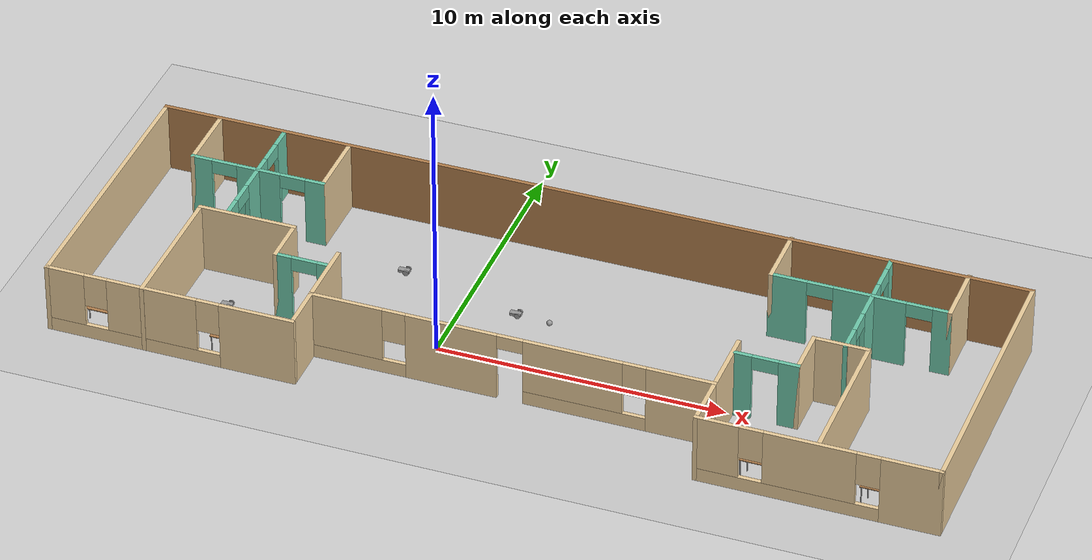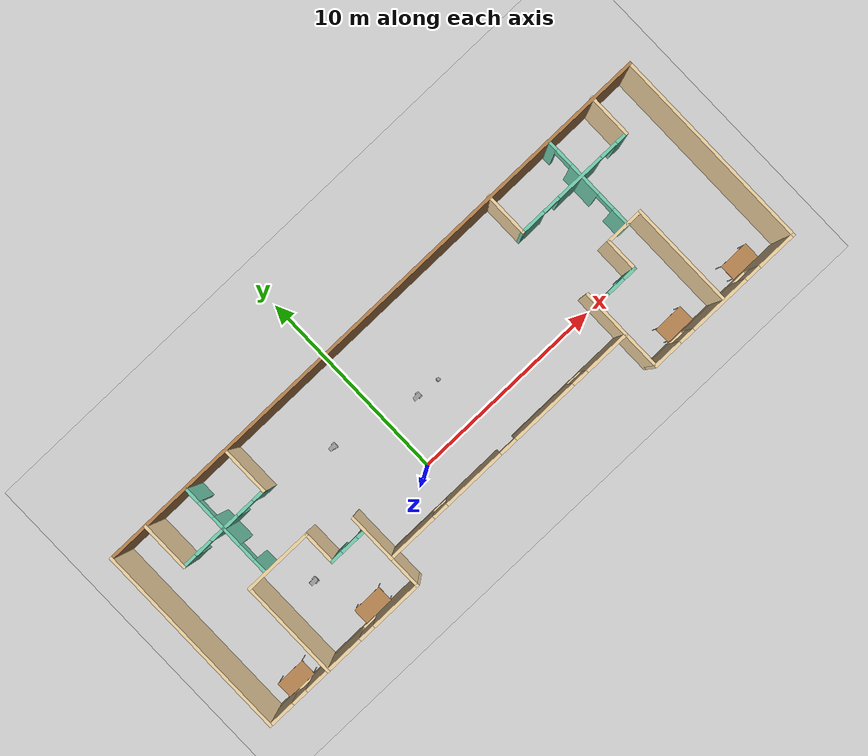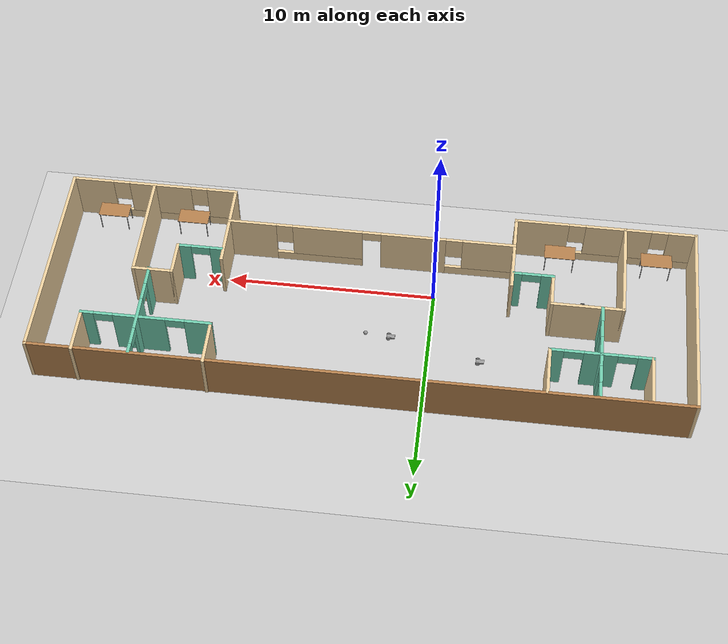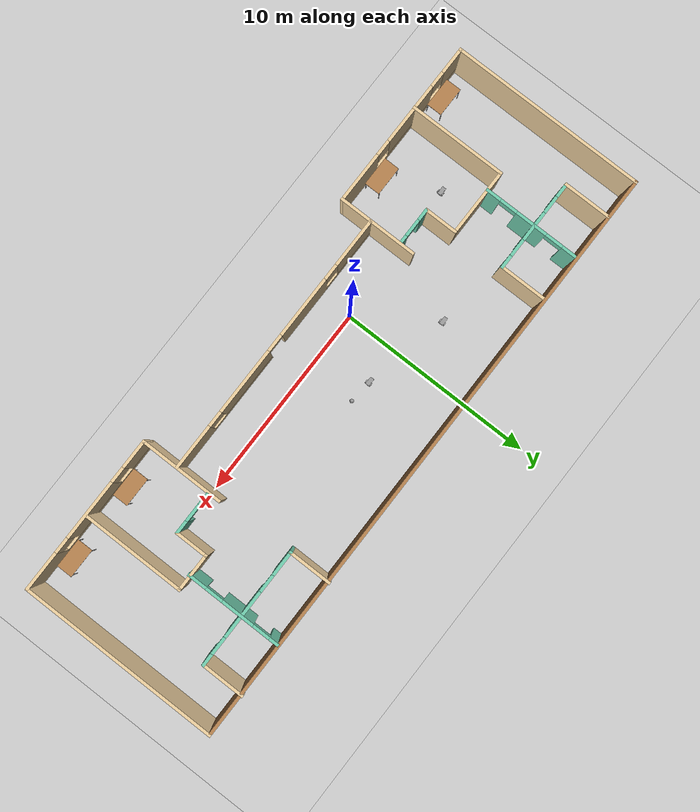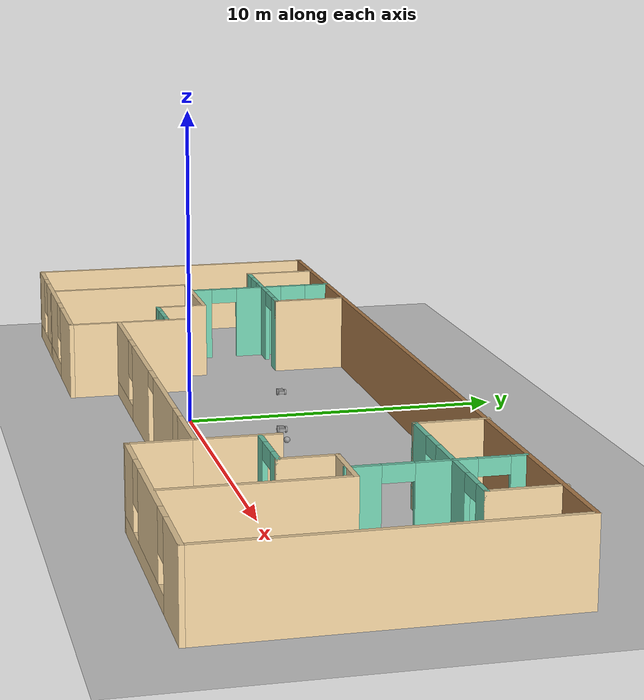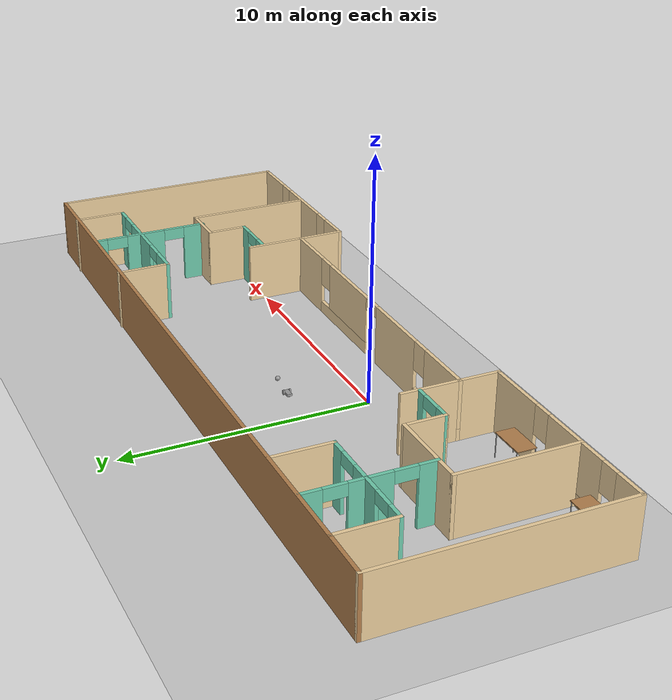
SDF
<sdf version="1.6">
 <world name="default">
  <plugin name="hello" filename="libhello.so"/>
  <light name="sun" type="directional">
   <pose>0 0 10 0 -0 0</pose>
   <diffuse>0.8 0.8 0.8 1</diffuse>
   <specular>0.2 0.2 0.2 1</specular>
   <attenuation>
    <range>1000</range>
    <constant>0.9</constant>
    <linear>0.01</linear>
    <quadratic>0.001</quadratic>
   </attenuation>
   <direction>-0.5 0.1 -0.9</direction>
  </light>
  <model name="ground_plane">
   <static>1</static>
   <link name="link">
    <collision name="collision">
     <geometry><plane><normal>0 0 1</normal><size>100 100</size></plane></geometry>
     <surface>
      <contact><collide_bitmask>65535</collide_bitmask></contact>
      <friction><ode><mu>100</mu><mu2>50</mu2></ode></friction>
     </surface>
    </collision>
    <visual name="visual">
     <cast_shadows>0</cast_shadows>
     <geometry><plane><normal>0 0 1</normal><size>100 100</size></plane></geometry>
     <material>
      <script><uri>file://media/materials/scripts/gazebo.material</uri><name>Gazebo/Grey</name></script>
     </material>
    </visual>
   </link>
  </model>
  <gravity>0 0 -9.8</gravity>
  <magnetic_field>6e-06 2.3e-05 -4.2e-05</magnetic_field>
  <atmosphere type="adiabatic"/>
  <physics name="default_physics" default="0" type="ode">
   <max_step_size>0.001</max_step_size>
   <real_time_factor>1</real_time_factor>
   <real_time_update_rate>1000</real_time_update_rate>
  </physics>
  <scene><ambient>0.4 0.4 0.4 1</ambient><background>0.7 0.7 0.7 1</background><shadows>1</shadows></scene>
  <spherical_coordinates>
   <surface_model>EARTH_WGS84</surface_model>
   <latitude_deg>0</latitude_deg>
   <longitude_deg>0</longitude_deg>
   <elevation>0</elevation>
   <heading_deg>0</heading_deg>
  </spherical_coordinates>
  <model name="mybuilding">
   <pose>2.9576 1.50841 0 0 -0 0</pose>
   <link name="Wall_11">
    <collision name="Wall_11_Collision">
     <geometry><box><size>10 0.15 2.5</size></box></geometry>
     <pose>0 0 1.25 0 -0 0</pose>
    </collision>
    <visual name="Wall_11_Visual">
     <pose>0 0 1.25 0 -0 0</pose>
     <geometry><box><size>10 0.15 2.5</size></box></geometry>
     <material>
      <script><uri>file://media/materials/scripts/gazebo.material</uri><name>Gazebo/Grey</name></script>
      <ambient>0.921569 0.807843 0.615686 1</ambient>
     </material>
     <meta><layer>0</layer></meta>
    </visual>
    <pose>-15.3 0.098461 0 0 0 -1.5708</pose>
   </link>
   <link name="Wall_15">
    <collision name="Wall_15_Collision">
     <geometry><box><size>2.5 0.15 2.5</size></box></geometry>
     <pose>0 0 1.25 0 -0 0</pose>
    </collision>
    <visual name="Wall_15_Visual">
     <pose>0 0 1.25 0 -0 0</pose>
     <geometry><box><size>2.5 0.15 2.5</size></box></geometry>
     <material>
      <script><uri>file://media/materials/scripts/gazebo.material</uri><name>Gazebo/Grey</name></script>
      <ambient>0.921569 0.807843 0.615686 1</ambient>
     </material>
     <meta><layer>0</layer></meta>
    </visual>
    <pose>-6.65 -2.05154 0 0 -0 1.5708</pose>
   </link>
   <link name="Wall_19">
    <pose>-7.64549 -1.58136 0 0 -0 3.14159</pose>
    <visual name="Wall_19_Visual_0">
     <pose>-0.774273 0 1.25 0 -0 0</pose>
     <geometry><box><size>0.451455 0.15 2.5</size></box></geometry>
     <material>
      <script><uri>file://media/materials/scripts/gazebo.material</uri><name>Gazebo/Grey</name></script>
      <ambient>0.435294 0.796078 0.67451 1</ambient>
     </material>
     <meta><layer>0</layer></meta>
    </visual>
    <collision name="Wall_19_Collision_0">
     <geometry><box><size>0.451455 0.15 2.5</size></box></geometry>
     <pose>-0.774273 0 1.25 0 -0 0</pose>
    </collision>
    <visual name="Wall_19_Visual_1">
     <pose>0.675727 0 1.25 0 -0 0</pose>
     <geometry><box><size>0.648545 0.15 2.5</size></box></geometry>
     <material>
      <script><uri>file://media/materials/scripts/gazebo.material</uri><name>Gazebo/Grey</name></script>
      <ambient>0.435294 0.796078 0.67451 1</ambient>
     </material>
     <meta><layer>0</layer></meta>
    </visual>
    <collision name="Wall_19_Collision_1">
     <geometry><box><size>0.648545 0.15 2.5</size></box></geometry>
     <pose>0.675727 0 1.25 0 -0 0</pose>
    </collision>
    <visual name="Wall_19_Visual_2">
     <pose>-0.098545 0 2.25 0 -0 0</pose>
     <geometry><box><size>0.9 0.15 0.5</size></box></geometry>
     <material>
      <script><uri>file://media/materials/scripts/gazebo.material</uri><name>Gazebo/Grey</name></script>
      <ambient>0.435294 0.796078 0.67451 1</ambient>
     </material>
     <meta><layer>0</layer></meta>
    </visual>
    <collision name="Wall_19_Collision_2">
     <geometry><box><size>0.9 0.15 0.5</size></box></geometry>
     <pose>-0.098545 0 2.25 0 -0 0</pose>
    </collision>
   </link>
   <link name="Wall_20">
    <collision name="Wall_20_Collision">
     <geometry><box><size>1.75 0.15 2.5</size></box></geometry>
     <pose>0 0 1.25 0 -0 0</pose>
    </collision>
    <visual name="Wall_20_Visual">
     <pose>0 0 1.25 0 -0 0</pose>
     <geometry><box><size>1.75 0.15 2.5</size></box></geometry>
     <material>
      <script><uri>file://media/materials/scripts/gazebo.material</uri><name>Gazebo/Grey</name></script>
      <ambient>0.921569 0.807843 0.615686 1</ambient>
     </material>
     <meta><layer>0</layer></meta>
    </visual>
    <pose>-8.57049 -0.781363 0 0 -0 1.5708</pose>
   </link>
   <link name="Wall_21">
    <collision name="Wall_21_Collision">
     <geometry><box><size>3.5 0.15 2.5</size></box></geometry>
     <pose>0 0 1.25 0 -0 0</pose>
    </collision>
    <visual name="Wall_21_Visual">
     <pose>0 0 1.25 0 -0 0</pose>
     <geometry><box><size>3.5 0.15 2.5</size></box></geometry>
     <material>
      <script><uri>file://media/materials/scripts/gazebo.material</uri><name>Gazebo/Grey</name></script>
      <ambient>0.921569 0.807843 0.615686 1</ambient>
     </material>
     <meta><layer>0</layer></meta>
    </visual>
    <pose>-10.2455 0.018637 0 0 -0 3.14159</pose>
   </link>
   <link name="Wall_24">
    <collision name="Wall_24_Collision">
     <geometry><box><size>5 0.15 2.5</size></box></geometry>
     <pose>0 0 1.25 0 -0 0</pose>
    </collision>
    <visual name="Wall_24_Visual">
     <pose>0 0 1.25 0 -0 0</pose>
     <geometry><box><size>5 0.15 2.5</size></box></geometry>
     <material>
      <script><uri>file://media/materials/scripts/gazebo.material</uri><name>Gazebo/Grey</name></script>
      <ambient>0.921569 0.807843 0.615686 1</ambient>
     </material>
     <meta><layer>0</layer></meta>
    </visual>
    <pose>-11.9205 -2.40636 0 0 0 -1.5708</pose>
   </link>
   <link name="Wall_26">
    <pose>-10.9495 1.33646 0 0 -0 1.5708</pose>
    <visual name="Wall_26_Visual_0">
     <pose>-0.979241 0 1.25 0 -0 0</pose>
     <geometry><box><size>0.791517 0.15 2.5</size></box></geometry>
     <material>
      <script><uri>file://media/materials/scripts/gazebo.material</uri><name>Gazebo/Grey</name></script>
      <ambient>0.435294 0.796078 0.67451 1</ambient>
     </material>
     <meta><layer>0</layer></meta>
    </visual>
    <collision name="Wall_26_Collision_0">
     <geometry><box><size>0.791517 0.15 2.5</size></box></geometry>
     <pose>-0.979241 0 1.25 0 -0 0</pose>
    </collision>
    <visual name="Wall_26_Visual_1">
     <pose>0.845759 0 1.25 0 -0 0</pose>
     <geometry><box><size>1.05848 0.15 2.5</size></box></geometry>
     <material>
      <script><uri>file://media/materials/scripts/gazebo.material</uri><name>Gazebo/Grey</name></script>
      <ambient>0.435294 0.796078 0.67451 1</ambient>
     </material>
     <meta><layer>0</layer></meta>
    </visual>
    <collision name="Wall_26_Collision_1">
     <geometry><box><size>1.05848 0.15 2.5</size></box></geometry>
     <pose>0.845759 0 1.25 0 -0 0</pose>
    </collision>
    <visual name="Wall_26_Visual_2">
     <pose>-0.133483 0 2.25 0 -0 0</pose>
     <geometry><box><size>0.9 0.15 0.5</size></box></geometry>
     <material>
      <script><uri>file://media/materials/scripts/gazebo.material</uri><name>Gazebo/Grey</name></script>
      <ambient>0.435294 0.796078 0.67451 1</ambient>
     </material>
     <meta><layer>0</layer></meta>
    </visual>
    <collision name="Wall_26_Collision_2">
     <geometry><box><size>0.9 0.15 0.5</size></box></geometry>
     <pose>-0.133483 0 2.25 0 -0 0</pose>
    </collision>
   </link>
   <link name="Wall_27">
    <pose>-12.1245 2.63646 0 0 -0 3.14159</pose>
    <visual name="Wall_27_Visual_0">
     <pose>-0.837629 0 1.25 0 -0 0</pose>
     <geometry><box><size>0.824741 0.15 2.5</size></box></geometry>
     <material>
      <script><uri>file://media/materials/scripts/gazebo.material</uri><name>Gazebo/Grey</name></script>
      <ambient>0.435294 0.796078 0.67451 1</ambient>
     </material>
     <meta><layer>0</layer></meta>
    </visual>
    <collision name="Wall_27_Collision_0">
     <geometry><box><size>0.824741 0.15 2.5</size></box></geometry>
     <pose>-0.837629 0 1.25 0 -0 0</pose>
    </collision>
    <visual name="Wall_27_Visual_1">
     <pose>0.862371 0 1.25 0 -0 0</pose>
     <geometry><box><size>0.775259 0.15 2.5</size></box></geometry>
     <material>
      <script><uri>file://media/materials/scripts/gazebo.material</uri><name>Gazebo/Grey</name></script>
      <ambient>0.435294 0.796078 0.67451 1</ambient>
     </material>
     <meta><layer>0</layer></meta>
    </visual>
    <collision name="Wall_27_Collision_1">
     <geometry><box><size>0.775259 0.15 2.5</size></box></geometry>
     <pose>0.862371 0 1.25 0 -0 0</pose>
    </collision>
    <visual name="Wall_27_Visual_2">
     <pose>0.024741 0 2.25 0 -0 0</pose>
     <geometry><box><size>0.9 0.15 0.5</size></box></geometry>
     <material>
      <script><uri>file://media/materials/scripts/gazebo.material</uri><name>Gazebo/Grey</name></script>
      <ambient>0.435294 0.796078 0.67451 1</ambient>
     </material>
     <meta><layer>0</layer></meta>
    </visual>
    <collision name="Wall_27_Collision_2">
     <geometry><box><size>0.9 0.15 0.5</size></box></geometry>
     <pose>0.024741 0 2.25 0 -0 0</pose>
    </collision>
   </link>
   <link name="Wall_28">
    <collision name="Wall_28_Collision">
     <geometry><box><size>2.5 0.15 2.5</size></box></geometry>
     <pose>0 0 1.25 0 -0 0</pose>
    </collision>
    <visual name="Wall_28_Visual">
     <pose>0 0 1.25 0 -0 0</pose>
     <geometry><box><size>2.5 0.15 2.5</size></box></geometry>
     <material>
      <script><uri>file://media/materials/scripts/gazebo.material</uri><name>Gazebo/Grey</name></script>
      <ambient>0.921569 0.807843 0.615686 1</ambient>
     </material>
     <meta><layer>0</layer></meta>
    </visual>
    <pose>-13.2995 3.81146 0 0 -0 1.5708</pose>
   </link>
   <link name="Wall_3">
    <collision name="Wall_3_Collision">
     <geometry><box><size>30.75 0.15 2.5</size></box></geometry>
     <pose>0 0 1.25 0 -0 0</pose>
    </collision>
    <visual name="Wall_3_Visual">
     <pose>0 0 1.25 0 -0 0</pose>
     <geometry><box><size>30.75 0.15 2.5</size></box></geometry>
     <material>
      <script><uri>file://media/materials/scripts/gazebo.material</uri><name>Gazebo/Wood</name></script>
      <ambient>0.921569 0.807843 0.615686 1</ambient>
     </material>
     <meta><layer>0</layer></meta>
    </visual>
    <pose>0 5.02346 0 0 -0 0</pose>
   </link>
   <link name="Wall_33">
    <pose>-10.9495 3.81146 0 0 -0 1.5708</pose>
    <visual name="Wall_33_Visual_0">
     <pose>-0.884642 0 1.25 0 -0 0</pose>
     <geometry><box><size>0.730717 0.15 2.5</size></box></geometry>
     <material>
      <script><uri>file://media/materials/scripts/gazebo.material</uri><name>Gazebo/Grey</name></script>
      <ambient>0.435294 0.796078 0.67451 1</ambient>
     </material>
     <meta><layer>0</layer></meta>
    </visual>
    <collision name="Wall_33_Collision_0">
     <geometry><box><size>0.730717 0.15 2.5</size></box></geometry>
     <pose>-0.884642 0 1.25 0 -0 0</pose>
    </collision>
    <visual name="Wall_33_Visual_1">
     <pose>0.815358 0 1.25 0 -0 0</pose>
     <geometry><box><size>0.869283 0.15 2.5</size></box></geometry>
     <material>
      <script><uri>file://media/materials/scripts/gazebo.material</uri><name>Gazebo/Grey</name></script>
      <ambient>0.435294 0.796078 0.67451 1</ambient>
     </material>
     <meta><layer>0</layer></meta>
    </visual>
    <collision name="Wall_33_Collision_1">
     <geometry><box><size>0.869283 0.15 2.5</size></box></geometry>
     <pose>0.815358 0 1.25 0 -0 0</pose>
    </collision>
    <visual name="Wall_33_Visual_2">
     <pose>-0.069283 0 2.25 0 -0 0</pose>
     <geometry><box><size>0.9 0.15 0.5</size></box></geometry>
     <material>
      <script><uri>file://media/materials/scripts/gazebo.material</uri><name>Gazebo/Grey</name></script>
      <ambient>0.435294 0.796078 0.67451 1</ambient>
     </material>
     <meta><layer>0</layer></meta>
    </visual>
    <collision name="Wall_33_Collision_2">
     <geometry><box><size>0.9 0.15 0.5</size></box></geometry>
     <pose>-0.069283 0 2.25 0 -0 0</pose>
    </collision>
   </link>
   <link name="Wall_35">
    <pose>-9.7745 2.63646 0 0 -0 0</pose>
    <visual name="Wall_35_Visual_0">
     <pose>-0.807446 0 1.25 0 -0 0</pose>
     <geometry><box><size>0.885108 0.15 2.5</size></box></geometry>
     <material>
      <script><uri>file://media/materials/scripts/gazebo.material</uri><name>Gazebo/Grey</name></script>
      <ambient>0.435294 0.796078 0.67451 1</ambient>
     </material>
     <meta><layer>0</layer></meta>
    </visual>
    <collision name="Wall_35_Collision_0">
     <geometry><box><size>0.885108 0.15 2.5</size></box></geometry>
     <pose>-0.807446 0 1.25 0 -0 0</pose>
    </collision>
    <visual name="Wall_35_Visual_1">
     <pose>0.892554 0 1.25 0 -0 0</pose>
     <geometry><box><size>0.714892 0.15 2.5</size></box></geometry>
     <material>
      <script><uri>file://media/materials/scripts/gazebo.material</uri><name>Gazebo/Grey</name></script>
      <ambient>0.435294 0.796078 0.67451 1</ambient>
     </material>
     <meta><layer>0</layer></meta>
    </visual>
    <collision name="Wall_35_Collision_1">
     <geometry><box><size>0.714892 0.15 2.5</size></box></geometry>
     <pose>0.892554 0 1.25 0 -0 0</pose>
    </collision>
    <visual name="Wall_35_Visual_2">
     <pose>0.085108 0 2.25 0 -0 0</pose>
     <geometry><box><size>0.9 0.15 0.5</size></box></geometry>
     <material>
      <script><uri>file://media/materials/scripts/gazebo.material</uri><name>Gazebo/Grey</name></script>
      <ambient>0.435294 0.796078 0.67451 1</ambient>
     </material>
     <meta><layer>0</layer></meta>
    </visual>
    <collision name="Wall_35_Collision_2">
     <geometry><box><size>0.9 0.15 0.5</size></box></geometry>
     <pose>0.085108 0 2.25 0 -0 0</pose>
    </collision>
   </link>
   <link name="Wall_36">
    <collision name="Wall_36_Collision">
     <geometry><box><size>2.5 0.15 2.5</size></box></geometry>
     <pose>0 0 1.25 0 -0 0</pose>
    </collision>
    <visual name="Wall_36_Visual">
     <pose>0 0 1.25 0 -0 0</pose>
     <geometry><box><size>2.5 0.15 2.5</size></box></geometry>
     <material>
      <script><uri>file://media/materials/scripts/gazebo.material</uri><name>Gazebo/Grey</name></script>
      <ambient>0.921569 0.807843 0.615686 1</ambient>
     </material>
     <meta><layer>0</layer></meta>
    </visual>
    <pose>-8.5995 3.81146 0 0 -0 1.5708</pose>
   </link>
   <link name="Wall_38">
    <collision name="Wall_38_Collision">
     <geometry><box><size>2.5 0.15 2.5</size></box></geometry>
     <pose>0 0 1.25 0 -0 0</pose>
    </collision>
    <visual name="Wall_38_Visual">
     <pose>0 0 1.25 0 -0 0</pose>
     <geometry><box><size>2.5 0.15 2.5</size></box></geometry>
     <material>
      <script><uri>file://media/materials/scripts/gazebo.material</uri><name>Gazebo/Grey</name></script>
      <ambient>0.921569 0.807843 0.615686 1</ambient>
     </material>
     <meta><layer>0</layer></meta>
    </visual>
    <pose>7.2 -2.05154 0 0 -0 1.5708</pose>
   </link>
   <link name="Wall_4">
    <collision name="Wall_4_Collision">
     <geometry><box><size>10.25 0.15 2.5</size></box></geometry>
     <pose>0 0 1.25 0 -0 0</pose>
    </collision>
    <visual name="Wall_4_Visual">
     <pose>0 0 1.25 0 -0 0</pose>
     <geometry><box><size>10.25 0.15 2.5</size></box></geometry>
     <material>
      <script><uri>file://media/materials/scripts/gazebo.material</uri><name>Gazebo/Grey</name></script>
      <ambient>0.921569 0.807843 0.615686 1</ambient>
     </material>
     <meta><layer>0</layer></meta>
    </visual>
    <pose>15.3 -0.026539 0 0 0 -1.5708</pose>
   </link>
   <link name="Wall_41">
    <pose>8.3574 -1.44801 0 0 -0 0</pose>
    <visual name="Wall_41_Visual_0">
     <pose>-0.810611 0 1.25 0 -0 0</pose>
     <geometry><box><size>0.628777 0.15 2.5</size></box></geometry>
     <material>
      <script><uri>file://media/materials/scripts/gazebo.material</uri><name>Gazebo/Grey</name></script>
      <ambient>0.435294 0.796078 0.67451 1</ambient>
     </material>
     <meta><layer>0</layer></meta>
    </visual>
    <collision name="Wall_41_Collision_0">
     <geometry><box><size>0.628777 0.15 2.5</size></box></geometry>
     <pose>-0.810611 0 1.25 0 -0 0</pose>
    </collision>
    <visual name="Wall_41_Visual_1">
     <pose>0.764389 0 1.25 0 -0 0</pose>
     <geometry><box><size>0.721223 0.15 2.5</size></box></geometry>
     <material>
      <script><uri>file://media/materials/scripts/gazebo.material</uri><name>Gazebo/Grey</name></script>
      <ambient>0.435294 0.796078 0.67451 1</ambient>
     </material>
     <meta><layer>0</layer></meta>
    </visual>
    <collision name="Wall_41_Collision_1">
     <geometry><box><size>0.721223 0.15 2.5</size></box></geometry>
     <pose>0.764389 0 1.25 0 -0 0</pose>
    </collision>
    <visual name="Wall_41_Visual_2">
     <pose>-0.046223 0 2.25 0 -0 0</pose>
     <geometry><box><size>0.9 0.15 0.5</size></box></geometry>
     <material>
      <script><uri>file://media/materials/scripts/gazebo.material</uri><name>Gazebo/Grey</name></script>
      <ambient>0.435294 0.796078 0.67451 1</ambient>
     </material>
     <meta><layer>0</layer></meta>
    </visual>
    <collision name="Wall_41_Collision_2">
     <geometry><box><size>0.9 0.15 0.5</size></box></geometry>
     <pose>-0.046223 0 2.25 0 -0 0</pose>
    </collision>
   </link>
   <link name="Wall_42">
    <collision name="Wall_42_Collision">
     <geometry><box><size>1.75 0.15 2.5</size></box></geometry>
     <pose>0 0 1.25 0 -0 0</pose>
    </collision>
    <visual name="Wall_42_Visual">
     <pose>0 0 1.25 0 -0 0</pose>
     <geometry><box><size>1.75 0.15 2.5</size></box></geometry>
     <material>
      <script><uri>file://media/materials/scripts/gazebo.material</uri><name>Gazebo/Grey</name></script>
      <ambient>0.921569 0.807843 0.615686 1</ambient>
     </material>
     <meta><layer>0</layer></meta>
    </visual>
    <pose>9.4074 -0.648014 0 0 -0 1.5708</pose>
   </link>
   <link name="Wall_43">
    <collision name="Wall_43_Collision">
     <geometry><box><size>2 0.15 2.5</size></box></geometry>
     <pose>0 0 1.25 0 -0 0</pose>
    </collision>
    <visual name="Wall_43_Visual">
     <pose>0 0 1.25 0 -0 0</pose>
     <geometry><box><size>2 0.15 2.5</size></box></geometry>
     <material>
      <script><uri>file://media/materials/scripts/gazebo.material</uri><name>Gazebo/Grey</name></script>
      <ambient>0.921569 0.807843 0.615686 1</ambient>
     </material>
     <meta><layer>0</layer></meta>
    </visual>
    <pose>10.3324 0.151986 0 0 -0 0</pose>
   </link>
   <link name="Wall_44">
    <collision name="Wall_44_Collision">
     <geometry><box><size>5.25 0.15 2.5</size></box></geometry>
     <pose>0 0 1.25 0 -0 0</pose>
    </collision>
    <visual name="Wall_44_Visual">
     <pose>0 0 1.25 0 -0 0</pose>
     <geometry><box><size>5.25 0.15 2.5</size></box></geometry>
     <material>
      <script><uri>file://media/materials/scripts/gazebo.material</uri><name>Gazebo/Grey</name></script>
      <ambient>0.921569 0.807843 0.615686 1</ambient>
     </material>
     <meta><layer>0</layer></meta>
    </visual>
    <pose>11.2574 -2.39801 0 0 0 -1.5708</pose>
   </link>
   <link name="Wall_48">
    <pose>10.5012 2.52828 0 0 -0 1.5708</pose>
    <visual name="Wall_48_Visual_0">
     <pose>-2.00311 0 1.25 0 -0 0</pose>
     <geometry><box><size>0.993788 0.15 2.5</size></box></geometry>
     <material>
      <script><uri>file://media/materials/scripts/gazebo.material</uri><name>Gazebo/Grey</name></script>
      <ambient>0.435294 0.796078 0.67451 1</ambient>
     </material>
     <meta><layer>0</layer></meta>
    </visual>
    <collision name="Wall_48_Collision_0">
     <geometry><box><size>0.993788 0.15 2.5</size></box></geometry>
     <pose>-2.00311 0 1.25 0 -0 0</pose>
    </collision>
    <visual name="Wall_48_Visual_1">
     <pose>0.244136 0 1.25 0 -0 0</pose>
     <geometry><box><size>1.7007 0.15 2.5</size></box></geometry>
     <material>
      <script><uri>file://media/materials/scripts/gazebo.material</uri><name>Gazebo/Grey</name></script>
      <ambient>0.435294 0.796078 0.67451 1</ambient>
     </material>
     <meta><layer>0</layer></meta>
    </visual>
    <collision name="Wall_48_Collision_1">
     <geometry><box><size>1.7007 0.15 2.5</size></box></geometry>
     <pose>0.244136 0 1.25 0 -0 0</pose>
    </collision>
    <visual name="Wall_48_Visual_2">
     <pose>2.24724 0 1.25 0 -0 0</pose>
     <geometry><box><size>0.505516 0.15 2.5</size></box></geometry>
     <material>
      <script><uri>file://media/materials/scripts/gazebo.material</uri><name>Gazebo/Grey</name></script>
      <ambient>0.435294 0.796078 0.67451 1</ambient>
     </material>
     <meta><layer>0</layer></meta>
    </visual>
    <collision name="Wall_48_Collision_2">
     <geometry><box><size>0.505516 0.15 2.5</size></box></geometry>
     <pose>2.24724 0 1.25 0 -0 0</pose>
    </collision>
    <visual name="Wall_48_Visual_3">
     <pose>-1.05621 0 2.25 0 -0 0</pose>
     <geometry><box><size>0.9 0.15 0.5</size></box></geometry>
     <material>
      <script><uri>file://media/materials/scripts/gazebo.material</uri><name>Gazebo/Grey</name></script>
      <ambient>0.435294 0.796078 0.67451 1</ambient>
     </material>
     <meta><layer>0</layer></meta>
    </visual>
    <collision name="Wall_48_Collision_3">
     <geometry><box><size>0.9 0.15 0.5</size></box></geometry>
     <pose>-1.05621 0 2.25 0 -0 0</pose>
    </collision>
    <visual name="Wall_48_Visual_4">
     <pose>1.54448 0 2.25 0 -0 0</pose>
     <geometry><box><size>0.9 0.15 0.5</size></box></geometry>
     <material>
      <script><uri>file://media/materials/scripts/gazebo.material</uri><name>Gazebo/Grey</name></script>
      <ambient>0.435294 0.796078 0.67451 1</ambient>
     </material>
     <meta><layer>0</layer></meta>
    </visual>
    <collision name="Wall_48_Collision_4">
     <geometry><box><size>0.9 0.15 0.5</size></box></geometry>
     <pose>1.54448 0 2.25 0 -0 0</pose>
    </collision>
   </link>
   <link name="Wall_5">
    <pose>11.25 -5.07654 0 0 -0 3.14159</pose>
    <visual name="Wall_5_Visual_0">
     <pose>-3.09721 0 1.25 0 -0 0</pose>
     <geometry><box><size>2.05557 0.15 2.5</size></box></geometry>
     <material>
      <script><uri>file://media/materials/scripts/gazebo.material</uri><name>Gazebo/Grey</name></script>
      <ambient>0.921569 0.807843 0.615686 1</ambient>
     </material>
     <meta><layer>0</layer></meta>
    </visual>
    <collision name="Wall_5_Collision_0">
     <geometry><box><size>2.05557 0.15 2.5</size></box></geometry>
     <pose>-3.09721 0 1.25 0 -0 0</pose>
    </collision>
    <visual name="Wall_5_Visual_1">
     <pose>1.02778 0 0.25 0 -0 0</pose>
     <geometry><box><size>6.19443 0.15 0.5</size></box></geometry>
     <material>
      <script><uri>file://media/materials/scripts/gazebo.material</uri><name>Gazebo/Grey</name></script>
      <ambient>0.921569 0.807843 0.615686 1</ambient>
     </material>
     <meta><layer>0</layer></meta>
    </visual>
    <collision name="Wall_5_Collision_1">
     <geometry><box><size>6.19443 0.15 0.5</size></box></geometry>
     <pose>1.02778 0 0.25 0 -0 0</pose>
    </collision>
    <visual name="Wall_5_Visual_2">
     <pose>0.269685 0 1.5 0 -0 0</pose>
     <geometry><box><size>3.07823 0.15 2</size></box></geometry>
     <material>
      <script><uri>file://media/materials/scripts/gazebo.material</uri><name>Gazebo/Grey</name></script>
      <ambient>0.921569 0.807843 0.615686 1</ambient>
     </material>
     <meta><layer>0</layer></meta>
    </visual>
    <collision name="Wall_5_Collision_2">
     <geometry><box><size>3.07823 0.15 2</size></box></geometry>
     <pose>0.269685 0 1.5 0 -0 0</pose>
    </collision>
    <visual name="Wall_5_Visual_3">
     <pose>3.3669 0 1.5 0 -0 0</pose>
     <geometry><box><size>1.5162 0.15 2</size></box></geometry>
     <material>
      <script><uri>file://media/materials/scripts/gazebo.material</uri><name>Gazebo/Grey</name></script>
      <ambient>0.921569 0.807843 0.615686 1</ambient>
     </material>
     <meta><layer>0</layer></meta>
    </visual>
    <collision name="Wall_5_Collision_3">
     <geometry><box><size>1.5162 0.15 2</size></box></geometry>
     <pose>3.3669 0 1.5 0 -0 0</pose>
    </collision>
    <visual name="Wall_5_Visual_4">
     <pose>-1.66943 0 1.9 0 -0 0</pose>
     <geometry><box><size>0.8 0.15 1.2</size></box></geometry>
     <material>
      <script><uri>file://media/materials/scripts/gazebo.material</uri><name>Gazebo/Grey</name></script>
      <ambient>0.921569 0.807843 0.615686 1</ambient>
     </material>
     <meta><layer>0</layer></meta>
    </visual>
    <collision name="Wall_5_Collision_4">
     <geometry><box><size>0.8 0.15 1.2</size></box></geometry>
     <pose>-1.66943 0 1.9 0 -0 0</pose>
    </collision>
    <visual name="Wall_5_Visual_5">
     <pose>2.2088 0 1.9 0 -0 0</pose>
     <geometry><box><size>0.8 0.15 1.2</size></box></geometry>
     <material>
      <script><uri>file://media/materials/scripts/gazebo.material</uri><name>Gazebo/Grey</name></script>
      <ambient>0.921569 0.807843 0.615686 1</ambient>
     </material>
     <meta><layer>0</layer></meta>
    </visual>
    <collision name="Wall_5_Collision_5">
     <geometry><box><size>0.8 0.15 1.2</size></box></geometry>
     <pose>2.2088 0 1.9 0 -0 0</pose>
    </collision>
   </link>
   <link name="Wall_52">
    <collision name="Wall_52_Collision">
     <geometry><box><size>2.25 0.15 2.5</size></box></geometry>
     <pose>0 0 1.25 0 -0 0</pose>
    </collision>
    <visual name="Wall_52_Visual">
     <pose>0 0 1.25 0 -0 0</pose>
     <geometry><box><size>2.25 0.15 2.5</size></box></geometry>
     <material>
      <script><uri>file://media/materials/scripts/gazebo.material</uri><name>Gazebo/Grey</name></script>
      <ambient>0.921569 0.807843 0.615686 1</ambient>
     </material>
     <meta><layer>0</layer></meta>
    </visual>
    <pose>7.03364 4.02654 0 0 0 -1.5708</pose>
   </link>
   <link name="Wall_53">
    <pose>10.0836 2.97654 0 0 -0 0</pose>
    <visual name="Wall_53_Visual_0">
     <pose>-2.46841 0 1.25 0 -0 0</pose>
     <geometry><box><size>1.31317 0.15 2.5</size></box></geometry>
     <material>
      <script><uri>file://media/materials/scripts/gazebo.material</uri><name>Gazebo/Grey</name></script>
      <ambient>0.435294 0.796078 0.67451 1</ambient>
     </material>
     <meta><layer>0</layer></meta>
    </visual>
    <collision name="Wall_53_Collision_0">
     <geometry><box><size>1.31317 0.15 2.5</size></box></geometry>
     <pose>-2.46841 0 1.25 0 -0 0</pose>
    </collision>
    <visual name="Wall_53_Visual_1">
     <pose>0.326343 0 1.25 0 -0 0</pose>
     <geometry><box><size>2.47634 0.15 2.5</size></box></geometry>
     <material>
      <script><uri>file://media/materials/scripts/gazebo.material</uri><name>Gazebo/Grey</name></script>
      <ambient>0.435294 0.796078 0.67451 1</ambient>
     </material>
     <meta><layer>0</layer></meta>
    </visual>
    <collision name="Wall_53_Collision_1">
     <geometry><box><size>2.47634 0.15 2.5</size></box></geometry>
     <pose>0.326343 0 1.25 0 -0 0</pose>
    </collision>
    <visual name="Wall_53_Visual_2">
     <pose>2.79476 0 1.25 0 -0 0</pose>
     <geometry><box><size>0.660486 0.15 2.5</size></box></geometry>
     <material>
      <script><uri>file://media/materials/scripts/gazebo.material</uri><name>Gazebo/Grey</name></script>
      <ambient>0.435294 0.796078 0.67451 1</ambient>
     </material>
     <meta><layer>0</layer></meta>
    </visual>
    <collision name="Wall_53_Collision_2">
     <geometry><box><size>0.660486 0.15 2.5</size></box></geometry>
     <pose>2.79476 0 1.25 0 -0 0</pose>
    </collision>
    <visual name="Wall_53_Visual_3">
     <pose>-1.36183 0 2.25 0 -0 0</pose>
     <geometry><box><size>0.9 0.15 0.5</size></box></geometry>
     <material>
      <script><uri>file://media/materials/scripts/gazebo.material</uri><name>Gazebo/Grey</name></script>
      <ambient>0.435294 0.796078 0.67451 1</ambient>
     </material>
     <meta><layer>0</layer></meta>
    </visual>
    <collision name="Wall_53_Collision_3">
     <geometry><box><size>0.9 0.15 0.5</size></box></geometry>
     <pose>-1.36183 0 2.25 0 -0 0</pose>
    </collision>
    <visual name="Wall_53_Visual_4">
     <pose>2.01451 0 2.25 0 -0 0</pose>
     <geometry><box><size>0.9 0.15 0.5</size></box></geometry>
     <material>
      <script><uri>file://media/materials/scripts/gazebo.material</uri><name>Gazebo/Grey</name></script>
      <ambient>0.435294 0.796078 0.67451 1</ambient>
     </material>
     <meta><layer>0</layer></meta>
    </visual>
    <collision name="Wall_53_Collision_4">
     <geometry><box><size>0.9 0.15 0.5</size></box></geometry>
     <pose>2.01451 0 2.25 0 -0 0</pose>
    </collision>
   </link>
   <link name="Wall_56">
    <collision name="Wall_56_Collision">
     <geometry><box><size>2.25 0.15 2.5</size></box></geometry>
     <pose>0 0 1.25 0 -0 0</pose>
    </collision>
    <visual name="Wall_56_Visual">
     <pose>0 0 1.25 0 -0 0</pose>
     <geometry><box><size>2.25 0.15 2.5</size></box></geometry>
     <material>
      <script><uri>file://media/materials/scripts/gazebo.material</uri><name>Gazebo/Grey</name></script>
      <ambient>0.921569 0.807843 0.615686 1</ambient>
     </material>
     <meta><layer>0</layer></meta>
    </visual>
    <pose>13.1336 4.02654 0 0 -0 1.5708</pose>
   </link>
   <link name="Wall_6">
    <collision name="Wall_6_Collision">
     <geometry><box><size>2 0.15 2.5</size></box></geometry>
     <pose>0 0 1.25 0 -0 0</pose>
    </collision>
    <visual name="Wall_6_Visual">
     <pose>0 0 1.25 0 -0 0</pose>
     <geometry><box><size>2 0.15 2.5</size></box></geometry>
     <material>
      <script><uri>file://media/materials/scripts/gazebo.material</uri><name>Gazebo/Grey</name></script>
      <ambient>0.921569 0.807843 0.615686 1</ambient>
     </material>
     <meta><layer>0</layer></meta>
    </visual>
    <pose>7.2 -4.15154 0 0 -0 1.5708</pose>
   </link>
   <link name="Wall_7">
    <pose>0.275 -3.22654 0 0 -0 3.14159</pose>
    <visual name="Wall_7_Visual_0">
     <pose>-5.81322 0 1.25 0 -0 0</pose>
     <geometry><box><size>2.37356 0.15 2.5</size></box></geometry>
     <material>
      <script><uri>file://media/materials/scripts/gazebo.material</uri><name>Gazebo/Grey</name></script>
      <ambient>0.921569 0.807843 0.615686 1</ambient>
     </material>
     <meta><layer>0</layer></meta>
    </visual>
    <collision name="Wall_7_Collision_0">
     <geometry><box><size>2.37356 0.15 2.5</size></box></geometry>
     <pose>-5.81322 0 1.25 0 -0 0</pose>
    </collision>
    <visual name="Wall_7_Visual_1">
     <pose>2.04894 0 1.25 0 -0 0</pose>
     <geometry><box><size>3.1551 0.15 2.5</size></box></geometry>
     <material>
      <script><uri>file://media/materials/scripts/gazebo.material</uri><name>Gazebo/Grey</name></script>
      <ambient>0.921569 0.807843 0.615686 1</ambient>
     </material>
     <meta><layer>0</layer></meta>
    </visual>
    <collision name="Wall_7_Collision_1">
     <geometry><box><size>3.1551 0.15 2.5</size></box></geometry>
     <pose>2.04894 0 1.25 0 -0 0</pose>
    </collision>
    <visual name="Wall_7_Visual_2">
     <pose>-2.52753 0 0.25 0 -0 0</pose>
     <geometry><box><size>4.19784 0.15 0.5</size></box></geometry>
     <material>
      <script><uri>file://media/materials/scripts/gazebo.material</uri><name>Gazebo/Grey</name></script>
      <ambient>0.921569 0.807843 0.615686 1</ambient>
     </material>
     <meta><layer>0</layer></meta>
    </visual>
    <collision name="Wall_7_Collision_2">
     <geometry><box><size>4.19784 0.15 0.5</size></box></geometry>
     <pose>-2.52753 0 0.25 0 -0 0</pose>
    </collision>
    <visual name="Wall_7_Visual_3">
     <pose>5.31325 0 0.25 0 -0 0</pose>
     <geometry><box><size>3.37351 0.15 0.5</size></box></geometry>
     <material>
      <script><uri>file://media/materials/scripts/gazebo.material</uri><name>Gazebo/Grey</name></script>
      <ambient>0.921569 0.807843 0.615686 1</ambient>
     </material>
     <meta><layer>0</layer></meta>
    </visual>
    <collision name="Wall_7_Collision_3">
     <geometry><box><size>3.37351 0.15 0.5</size></box></geometry>
     <pose>5.31325 0 0.25 0 -0 0</pose>
    </collision>
    <visual name="Wall_7_Visual_4">
     <pose>-2.12753 0 1.5 0 -0 0</pose>
     <geometry><box><size>3.39784 0.15 2</size></box></geometry>
     <material>
      <script><uri>file://media/materials/scripts/gazebo.material</uri><name>Gazebo/Grey</name></script>
      <ambient>0.921569 0.807843 0.615686 1</ambient>
     </material>
     <meta><layer>0</layer></meta>
    </visual>
    <collision name="Wall_7_Collision_4">
     <geometry><box><size>3.39784 0.15 2</size></box></geometry>
     <pose>-2.12753 0 1.5 0 -0 0</pose>
    </collision>
    <visual name="Wall_7_Visual_5">
     <pose>-2.12753 0 1.5 0 -0 0</pose>
     <geometry><box><size>3.39784 0.15 2</size></box></geometry>
     <material>
      <script><uri>file://media/materials/scripts/gazebo.material</uri><name>Gazebo/Grey</name></script>
      <ambient>0.921569 0.807843 0.615686 1</ambient>
     </material>
     <meta><layer>0</layer></meta>
    </visual>
    <collision name="Wall_7_Collision_5">
     <geometry><box><size>3.39784 0.15 2</size></box></geometry>
     <pose>-2.12753 0 1.5 0 -0 0</pose>
    </collision>
    <visual name="Wall_7_Visual_6">
     <pose>5.71325 0 1.5 0 -0 0</pose>
     <geometry><box><size>2.57351 0.15 2</size></box></geometry>
     <material>
      <script><uri>file://media/materials/scripts/gazebo.material</uri><name>Gazebo/Grey</name></script>
      <ambient>0.921569 0.807843 0.615686 1</ambient>
     </material>
     <meta><layer>0</layer></meta>
    </visual>
    <collision name="Wall_7_Collision_6">
     <geometry><box><size>2.57351 0.15 2</size></box></geometry>
     <pose>5.71325 0 1.5 0 -0 0</pose>
    </collision>
    <visual name="Wall_7_Visual_7">
     <pose>-4.22645 0 1.9 0 -0 0</pose>
     <geometry><box><size>0.8 0.15 1.2</size></box></geometry>
     <material>
      <script><uri>file://media/materials/scripts/gazebo.material</uri><name>Gazebo/Grey</name></script>
      <ambient>0.921569 0.807843 0.615686 1</ambient>
     </material>
     <meta><layer>0</layer></meta>
    </visual>
    <collision name="Wall_7_Collision_7">
     <geometry><box><size>0.8 0.15 1.2</size></box></geometry>
     <pose>-4.22645 0 1.9 0 -0 0</pose>
    </collision>
    <visual name="Wall_7_Visual_8">
     <pose>4.02649 0 1.9 0 -0 0</pose>
     <geometry><box><size>0.8 0.15 1.2</size></box></geometry>
     <material>
      <script><uri>file://media/materials/scripts/gazebo.material</uri><name>Gazebo/Grey</name></script>
      <ambient>0.921569 0.807843 0.615686 1</ambient>
     </material>
     <meta><layer>0</layer></meta>
    </visual>
    <collision name="Wall_7_Collision_8">
     <geometry><box><size>0.8 0.15 1.2</size></box></geometry>
     <pose>4.02649 0 1.9 0 -0 0</pose>
    </collision>
    <visual name="Wall_7_Visual_9">
     <pose>0.021391 0 2.25 0 -0 0</pose>
     <geometry><box><size>0.9 0.15 0.5</size></box></geometry>
     <material>
      <script><uri>file://media/materials/scripts/gazebo.material</uri><name>Gazebo/Grey</name></script>
      <ambient>0.921569 0.807843 0.615686 1</ambient>
     </material>
     <meta><layer>0</layer></meta>
    </visual>
    <collision name="Wall_7_Collision_9">
     <geometry><box><size>0.9 0.15 0.5</size></box></geometry>
     <pose>0.021391 0 2.25 0 -0 0</pose>
    </collision>
    <visual name="Wall_7_Visual_10">
     <pose>0.021391 0 2.25 0 -0 0</pose>
     <geometry><box><size>0.9 0.15 0.5</size></box></geometry>
     <material>
      <script><uri>file://media/materials/scripts/gazebo.material</uri><name>Gazebo/Grey</name></script>
      <ambient>0.921569 0.807843 0.615686 1</ambient>
     </material>
     <meta><layer>0</layer></meta>
    </visual>
    <collision name="Wall_7_Collision_10">
     <geometry><box><size>0.9 0.15 0.5</size></box></geometry>
     <pose>0.021391 0 2.25 0 -0 0</pose>
    </collision>
   </link>
   <link name="Wall_8">
    <collision name="Wall_8_Collision">
     <geometry><box><size>1.75 0.15 2.5</size></box></geometry>
     <pose>0 0 1.25 0 -0 0</pose>
    </collision>
    <visual name="Wall_8_Visual">
     <pose>0 0 1.25 0 -0 0</pose>
     <geometry><box><size>1.75 0.15 2.5</size></box></geometry>
     <material>
      <script><uri>file://media/materials/scripts/gazebo.material</uri><name>Gazebo/Grey</name></script>
      <ambient>0.921569 0.807843 0.615686 1</ambient>
     </material>
     <meta><layer>0</layer></meta>
    </visual>
    <pose>-6.65 -4.02654 0 0 0 -1.5708</pose>
   </link>
   <link name="Wall_9">
    <pose>-10.95 -4.82654 0 0 -0 3.14159</pose>
    <visual name="Wall_9_Visual_0">
     <pose>-3.05748 0 1.25 0 -0 0</pose>
     <geometry><box><size>2.63504 0.15 2.5</size></box></geometry>
     <material>
      <script><uri>file://media/materials/scripts/gazebo.material</uri><name>Gazebo/Grey</name></script>
      <ambient>0.921569 0.807843 0.615686 1</ambient>
     </material>
     <meta><layer>0</layer></meta>
    </visual>
    <collision name="Wall_9_Collision_0">
     <geometry><box><size>2.63504 0.15 2.5</size></box></geometry>
     <pose>-3.05748 0 1.25 0 -0 0</pose>
    </collision>
    <visual name="Wall_9_Visual_1">
     <pose>1.31752 0 0.25 0 -0 0</pose>
     <geometry><box><size>6.11496 0.15 0.5</size></box></geometry>
     <material>
      <script><uri>file://media/materials/scripts/gazebo.material</uri><name>Gazebo/Grey</name></script>
      <ambient>0.921569 0.807843 0.615686 1</ambient>
     </material>
     <meta><layer>0</layer></meta>
    </visual>
    <collision name="Wall_9_Collision_1">
     <geometry><box><size>6.11496 0.15 0.5</size></box></geometry>
     <pose>1.31752 0 0.25 0 -0 0</pose>
    </collision>
    <visual name="Wall_9_Visual_2">
     <pose>0.643793 0 1.5 0 -0 0</pose>
     <geometry><box><size>3.1675 0.15 2</size></box></geometry>
     <material>
      <script><uri>file://media/materials/scripts/gazebo.material</uri><name>Gazebo/Grey</name></script>
      <ambient>0.921569 0.807843 0.615686 1</ambient>
     </material>
     <meta><layer>0</layer></meta>
    </visual>
    <collision name="Wall_9_Collision_2">
     <geometry><box><size>3.1675 0.15 2</size></box></geometry>
     <pose>0.643793 0 1.5 0 -0 0</pose>
    </collision>
    <visual name="Wall_9_Visual_3">
     <pose>3.70127 0 1.5 0 -0 0</pose>
     <geometry><box><size>1.34746 0.15 2</size></box></geometry>
     <material>
      <script><uri>file://media/materials/scripts/gazebo.material</uri><name>Gazebo/Grey</name></script>
      <ambient>0.921569 0.807843 0.615686 1</ambient>
     </material>
     <meta><layer>0</layer></meta>
    </visual>
    <collision name="Wall_9_Collision_3">
     <geometry><box><size>1.34746 0.15 2</size></box></geometry>
     <pose>3.70127 0 1.5 0 -0 0</pose>
    </collision>
    <visual name="Wall_9_Visual_4">
     <pose>-1.33996 0 1.9 0 -0 0</pose>
     <geometry><box><size>0.8 0.15 1.2</size></box></geometry>
     <material>
      <script><uri>file://media/materials/scripts/gazebo.material</uri><name>Gazebo/Grey</name></script>
      <ambient>0.921569 0.807843 0.615686 1</ambient>
     </material>
     <meta><layer>0</layer></meta>
    </visual>
    <collision name="Wall_9_Collision_4">
     <geometry><box><size>0.8 0.15 1.2</size></box></geometry>
     <pose>-1.33996 0 1.9 0 -0 0</pose>
    </collision>
    <visual name="Wall_9_Visual_5">
     <pose>2.62754 0 1.9 0 -0 0</pose>
     <geometry><box><size>0.8 0.15 1.2</size></box></geometry>
     <material>
      <script><uri>file://media/materials/scripts/gazebo.material</uri><name>Gazebo/Grey</name></script>
      <ambient>0.921569 0.807843 0.615686 1</ambient>
     </material>
     <meta><layer>0</layer></meta>
    </visual>
    <collision name="Wall_9_Collision_5">
     <geometry><box><size>0.8 0.15 1.2</size></box></geometry>
     <pose>2.62754 0 1.9 0 -0 0</pose>
    </collision>
   </link>
   <static>1</static>
  </model>
  <model name="table">
   <static>1</static>
   <link name="link">
    <collision name="surface">
     <pose>0 0 1 0 -0 0</pose>
     <geometry><box><size>1.5 0.8 0.03</size></box></geometry>
     <surface><friction><ode><mu>0.6</mu><mu2>0.6</mu2></ode></friction></surface>
    </collision>
    <visual name="visual1">
     <pose>0 0 1 0 -0 0</pose>
     <geometry><box><size>1.5 0.8 0.03</size></box></geometry>
     <material>
      <script><uri>file://media/materials/scripts/gazebo.material</uri><name>Gazebo/Wood</name></script>
     </material>
    </visual>
    <collision name="front_left_leg">
     <pose>0.68 0.38 0.5 0 -0 0</pose>
     <geometry><cylinder><radius>0.02</radius><length>1</length></cylinder></geometry>
    </collision>
    <visual name="front_left_leg">
     <pose>0.68 0.38 0.5 0 -0 0</pose>
     <geometry><cylinder><radius>0.02</radius><length>1</length></cylinder></geometry>
     <material>
      <script><uri>file://media/materials/scripts/gazebo.material</uri><name>Gazebo/Grey</name></script>
     </material>
    </visual>
    <collision name="front_right_leg">
     <pose>0.68 -0.38 0.5 0 -0 0</pose>
     <geometry><cylinder><radius>0.02</radius><length>1</length></cylinder></geometry>
    </collision>
    <visual name="front_right_leg">
     <pose>0.68 -0.38 0.5 0 -0 0</pose>
     <geometry><cylinder><radius>0.02</radius><length>1</length></cylinder></geometry>
     <material>
      <script><uri>file://media/materials/scripts/gazebo.material</uri><name>Gazebo/Grey</name></script>
     </material>
    </visual>
    <collision name="back_right_leg">
     <pose>-0.68 -0.38 0.5 0 -0 0</pose>
     <geometry><cylinder><radius>0.02</radius><length>1</length></cylinder></geometry>
    </collision>
    <visual name="back_right_leg">
     <pose>-0.68 -0.38 0.5 0 -0 0</pose>
     <geometry><cylinder><radius>0.02</radius><length>1</length></cylinder></geometry>
     <material>
      <script><uri>file://media/materials/scripts/gazebo.material</uri><name>Gazebo/Grey</name></script>
     </material>
    </visual>
    <collision name="back_left_leg">
     <pose>-0.68 0.38 0.5 0 -0 0</pose>
     <geometry><cylinder><radius>0.02</radius><length>1</length></cylinder></geometry>
    </collision>
    <visual name="back_left_leg">
     <pose>-0.68 0.38 0.5 0 -0 0</pose>
     <geometry><cylinder><radius>0.02</radius><length>1</length></cylinder></geometry>
     <material>
      <script><uri>file://media/materials/scripts/gazebo.material</uri><name>Gazebo/Grey</name></script>
     </material>
    </visual>
   </link>
   <pose>12.2765 -2.98682 0 0 -0 0</pose>
  </model>
  <model name="table_0">
   <static>1</static>
   <link name="link">
    <collision name="surface">
     <pose>0 0 1 0 -0 0</pose>
     <geometry><box><size>1.5 0.8 0.03</size></box></geometry>
     <surface><friction><ode><mu>0.6</mu><mu2>0.6</mu2></ode></friction></surface>
    </collision>
    <visual name="visual1">
     <pose>0 0 1 0 -0 0</pose>
     <geometry><box><size>1.5 0.8 0.03</size></box></geometry>
     <material>
      <script><uri>file://media/materials/scripts/gazebo.material</uri><name>Gazebo/Wood</name></script>
     </material>
    </visual>
    <collision name="front_left_leg">
     <pose>0.68 0.38 0.5 0 -0 0</pose>
     <geometry><cylinder><radius>0.02</radius><length>1</length></cylinder></geometry>
    </collision>
    <visual name="front_left_leg">
     <pose>0.68 0.38 0.5 0 -0 0</pose>
     <geometry><cylinder><radius>0.02</radius><length>1</length></cylinder></geometry>
     <material>
      <script><uri>file://media/materials/scripts/gazebo.material</uri><name>Gazebo/Grey</name></script>
     </material>
    </visual>
    <collision name="front_right_leg">
     <pose>0.68 -0.38 0.5 0 -0 0</pose>
     <geometry><cylinder><radius>0.02</radius><length>1</length></cylinder></geometry>
    </collision>
    <visual name="front_right_leg">
     <pose>0.68 -0.38 0.5 0 -0 0</pose>
     <geometry><cylinder><radius>0.02</radius><length>1</length></cylinder></geometry>
     <material>
      <script><uri>file://media/materials/scripts/gazebo.material</uri><name>Gazebo/Grey</name></script>
     </material>
    </visual>
    <collision name="back_right_leg">
     <pose>-0.68 -0.38 0.5 0 -0 0</pose>
     <geometry><cylinder><radius>0.02</radius><length>1</length></cylinder></geometry>
    </collision>
    <visual name="back_right_leg">
     <pose>-0.68 -0.38 0.5 0 -0 0</pose>
     <geometry><cylinder><radius>0.02</radius><length>1</length></cylinder></geometry>
     <material>
      <script><uri>file://media/materials/scripts/gazebo.material</uri><name>Gazebo/Grey</name></script>
     </material>
    </visual>
    <collision name="back_left_leg">
     <pose>-0.68 0.38 0.5 0 -0 0</pose>
     <geometry><cylinder><radius>0.02</radius><length>1</length></cylinder></geometry>
    </collision>
    <visual name="back_left_leg">
     <pose>-0.68 0.38 0.5 0 -0 0</pose>
     <geometry><cylinder><radius>0.02</radius><length>1</length></cylinder></geometry>
     <material>
      <script><uri>file://media/materials/scripts/gazebo.material</uri><name>Gazebo/Grey</name></script>
     </material>
    </visual>
   </link>
   <pose>16.2886 -2.97188 0 0 -0 0</pose>
  </model>
  <model name="table_1">
   <static>1</static>
   <link name="link">
    <collision name="surface">
     <pose>0 0 1 0 -0 0</pose>
     <geometry><box><size>1.5 0.8 0.03</size></box></geometry>
     <surface><friction><ode><mu>0.6</mu><mu2>0.6</mu2></ode></friction></surface>
    </collision>
    <visual name="visual1">
     <pose>0 0 1 0 -0 0</pose>
     <geometry><box><size>1.5 0.8 0.03</size></box></geometry>
     <material>
      <script><uri>file://media/materials/scripts/gazebo.material</uri><name>Gazebo/Wood</name></script>
     </material>
    </visual>
    <collision name="front_left_leg">
     <pose>0.68 0.38 0.5 0 -0 0</pose>
     <geometry><cylinder><radius>0.02</radius><length>1</length></cylinder></geometry>
    </collision>
    <visual name="front_left_leg">
     <pose>0.68 0.38 0.5 0 -0 0</pose>
     <geometry><cylinder><radius>0.02</radius><length>1</length></cylinder></geometry>
     <material>
      <script><uri>file://media/materials/scripts/gazebo.material</uri><name>Gazebo/Grey</name></script>
     </material>
    </visual>
    <collision name="front_right_leg">
     <pose>0.68 -0.38 0.5 0 -0 0</pose>
     <geometry><cylinder><radius>0.02</radius><length>1</length></cylinder></geometry>
    </collision>
    <visual name="front_right_leg">
     <pose>0.68 -0.38 0.5 0 -0 0</pose>
     <geometry><cylinder><radius>0.02</radius><length>1</length></cylinder></geometry>
     <material>
      <script><uri>file://media/materials/scripts/gazebo.material</uri><name>Gazebo/Grey</name></script>
     </material>
    </visual>
    <collision name="back_right_leg">
     <pose>-0.68 -0.38 0.5 0 -0 0</pose>
     <geometry><cylinder><radius>0.02</radius><length>1</length></cylinder></geometry>
    </collision>
    <visual name="back_right_leg">
     <pose>-0.68 -0.38 0.5 0 -0 0</pose>
     <geometry><cylinder><radius>0.02</radius><length>1</length></cylinder></geometry>
     <material>
      <script><uri>file://media/materials/scripts/gazebo.material</uri><name>Gazebo/Grey</name></script>
     </material>
    </visual>
    <collision name="back_left_leg">
     <pose>-0.68 0.38 0.5 0 -0 0</pose>
     <geometry><cylinder><radius>0.02</radius><length>1</length></cylinder></geometry>
    </collision>
    <visual name="back_left_leg">
     <pose>-0.68 0.38 0.5 0 -0 0</pose>
     <geometry><cylinder><radius>0.02</radius><length>1</length></cylinder></geometry>
     <material>
      <script><uri>file://media/materials/scripts/gazebo.material</uri><name>Gazebo/Grey</name></script>
     </material>
    </visual>
   </link>
   <pose>-10.6647 -2.78045 0 0 -0 0</pose>
  </model>
  <model name="table_2">
   <static>1</static>
   <link name="link">
    <collision name="surface">
     <pose>0 0 1 0 -0 0</pose>
     <geometry><box><size>1.5 0.8 0.03</size></box></geometry>
     <surface><friction><ode><mu>0.6</mu><mu2>0.6</mu2></ode></friction></surface>
    </collision>
    <visual name="visual1">
     <pose>0 0 1 0 -0 0</pose>
     <geometry><box><size>1.5 0.8 0.03</size></box></geometry>
     <material>
      <script><uri>file://media/materials/scripts/gazebo.material</uri><name>Gazebo/Wood</name></script>
     </material>
    </visual>
    <collision name="front_left_leg">
     <pose>0.68 0.38 0.5 0 -0 0</pose>
     <geometry><cylinder><radius>0.02</radius><length>1</length></cylinder></geometry>
    </collision>
    <visual name="front_left_leg">
     <pose>0.68 0.38 0.5 0 -0 0</pose>
     <geometry><cylinder><radius>0.02</radius><length>1</length></cylinder></geometry>
     <material>
      <script><uri>file://media/materials/scripts/gazebo.material</uri><name>Gazebo/Grey</name></script>
     </material>
    </visual>
    <collision name="front_right_leg">
     <pose>0.68 -0.38 0.5 0 -0 0</pose>
     <geometry><cylinder><radius>0.02</radius><length>1</length></cylinder></geometry>
    </collision>
    <visual name="front_right_leg">
     <pose>0.68 -0.38 0.5 0 -0 0</pose>
     <geometry><cylinder><radius>0.02</radius><length>1</length></cylinder></geometry>
     <material>
      <script><uri>file://media/materials/scripts/gazebo.material</uri><name>Gazebo/Grey</name></script>
     </material>
    </visual>
    <collision name="back_right_leg">
     <pose>-0.68 -0.38 0.5 0 -0 0</pose>
     <geometry><cylinder><radius>0.02</radius><length>1</length></cylinder></geometry>
    </collision>
    <visual name="back_right_leg">
     <pose>-0.68 -0.38 0.5 0 -0 0</pose>
     <geometry><cylinder><radius>0.02</radius><length>1</length></cylinder></geometry>
     <material>
      <script><uri>file://media/materials/scripts/gazebo.material</uri><name>Gazebo/Grey</name></script>
     </material>
    </visual>
    <collision name="back_left_leg">
     <pose>-0.68 0.38 0.5 0 -0 0</pose>
     <geometry><cylinder><radius>0.02</radius><length>1</length></cylinder></geometry>
    </collision>
    <visual name="back_left_leg">
     <pose>-0.68 0.38 0.5 0 -0 0</pose>
     <geometry><cylinder><radius>0.02</radius><length>1</length></cylinder></geometry>
     <material>
      <script><uri>file://media/materials/scripts/gazebo.material</uri><name>Gazebo/Grey</name></script>
     </material>
    </visual>
   </link>
   <pose>-5.96146 -2.77053 0 0 -0 0</pose>
  </model>
  <model name="robot">
   <link name="link_0">
    <pose>-0.066667 0 0 0 -0 0</pose>
    <inertial>
     <mass>1</mass>
     <inertia>
      <ixx>0.166667</ixx>
      <ixy>0</ixy>
      <ixz>0</ixz>
      <iyy>0.166667</iyy>
      <iyz>0</iyz>
      <izz>0.166667</izz>
     </inertia>
    </inertial>
    <visual name="ModelPreview_0::link_0::visual_1">
     <pose>-0.15 0 -0.05 0 -0 0</pose>
     <geometry><sphere><radius>0.05</radius></sphere></geometry>
     <material>
      <lighting>1</lighting>
      <script><uri>file://media/materials/scripts/gazebo.material</uri><name>Gazebo/Grey</name></script>
      <shader type="pixel"><normal_map>__default__</normal_map></shader>
      <ambient>0.3 0.3 0.3 1</ambient>
      <diffuse>0.7 0.7 0.7 1</diffuse>
      <specular>0.01 0.01 0.01 1</specular>
      <emissive>0 0 0 1</emissive>
     </material>
    </visual>
    <visual name="visual">
     <geometry><box><size>0.4 0.2 0.1</size></box></geometry>
     <material>
      <lighting>1</lighting>
      <script><uri>file://media/materials/scripts/gazebo.material</uri><name>Gazebo/Grey</name></script>
      <shader type="pixel"><normal_map>__default__</normal_map></shader>
      <ambient>0.3 0.3 0.3 1</ambient>
      <diffuse>0.7 0.7 0.7 1</diffuse>
      <specular>0.01 0.01 0.01 1</specular>
      <emissive>0 0 0 1</emissive>
     </material>
    </visual>
    <collision name="collision_1">
     <pose>-0.15 0 -0.05 0 -0 0</pose>
     <geometry><sphere><radius>0.05</radius></sphere></geometry>
     <surface>
      <friction>
       <ode><mu>0</mu><mu2>0</mu2><fdir1>0 0 0</fdir1><slip1>1</slip1><slip2>1</slip2></ode>
       <torsional>
        <coefficient>1</coefficient>
        <patch_radius>0</patch_radius>
        <surface_radius>0</surface_radius>
        <use_patch_radius>1</use_patch_radius>
        <ode><slip>0</slip></ode>
       </torsional>
      </friction>
      <bounce><restitution_coefficient>0</restitution_coefficient><threshold>1e+06</threshold></bounce>
      <contact>
       <collide_without_contact>0</collide_without_contact>
       <collide_without_contact_bitmask>1</collide_without_contact_bitmask>
       <collide_bitmask>1</collide_bitmask>
       <ode>
        <soft_cfm>0</soft_cfm>
        <soft_erp>0.2</soft_erp>
        <kp>1e+13</kp>
        <kd>1</kd>
        <max_vel>0.01</max_vel>
        <min_depth>0</min_depth>
       </ode>
       <bullet>
        <split_impulse>1</split_impulse>
        <split_impulse_penetration_threshold>-0.01</split_impulse_penetration_threshold>
        <soft_cfm>0</soft_cfm>
        <soft_erp>0.2</soft_erp>
        <kp>1e+13</kp>
        <kd>1</kd>
       </bullet>
      </contact>
     </surface>
    </collision>
    <collision name="collision">
     <geometry><box><size>0.4 0.2 0.1</size></box></geometry>
     <surface>
      <friction>
       <ode><mu>1</mu><mu2>1</mu2><fdir1>0 0 0</fdir1><slip1>0</slip1><slip2>0</slip2></ode>
       <torsional>
        <coefficient>1</coefficient>
        <patch_radius>0</patch_radius>
        <surface_radius>0</surface_radius>
        <use_patch_radius>1</use_patch_radius>
        <ode><slip>0</slip></ode>
       </torsional>
      </friction>
      <bounce><restitution_coefficient>0</restitution_coefficient><threshold>1e+06</threshold></bounce>
      <contact>
       <collide_without_contact>0</collide_without_contact>
       <collide_without_contact_bitmask>1</collide_without_contact_bitmask>
       <collide_bitmask>1</collide_bitmask>
       <ode>
        <soft_cfm>0</soft_cfm>
        <soft_erp>0.2</soft_erp>
        <kp>1e+13</kp>
        <kd>1</kd>
        <max_vel>0.01</max_vel>
        <min_depth>0</min_depth>
       </ode>
       <bullet>
        <split_impulse>1</split_impulse>
        <split_impulse_penetration_threshold>-0.01</split_impulse_penetration_threshold>
        <soft_cfm>0</soft_cfm>
        <soft_erp>0.2</soft_erp>
        <kp>1e+13</kp>
        <kd>1</kd>
       </bullet>
      </contact>
     </surface>
    </collision>
   </link>
   <link name="link_2">
    <pose>0.033333 0.13 0 -0.000572 1.5707 1.57013</pose>
    <inertial>
     <mass>1</mass>
     <inertia><ixx>0.145833</ixx><ixy>0</ixy><ixz>0</ixz><iyy>0.145833</iyy><iyz>0</iyz><izz>0.125</izz></inertia>
    </inertial>
    <visual name="visual">
     <geometry><cylinder><radius>0.1</radius><length>0.05</length></cylinder></geometry>
     <material>
      <lighting>1</lighting>
      <script><uri>file://media/materials/scripts/gazebo.material</uri><name>Gazebo/Grey</name></script>
      <shader type="pixel"><normal_map>__default__</normal_map></shader>
      <ambient>0.3 0.3 0.3 1</ambient>
      <diffuse>0.7 0.7 0.7 1</diffuse>
      <specular>0.01 0.01 0.01 1</specular>
      <emissive>0 0 0 1</emissive>
     </material>
    </visual>
    <collision name="collision">
     <geometry><cylinder><radius>0.1</radius><length>0.05</length></cylinder></geometry>
     <surface>
      <friction>
       <ode><mu>1</mu><mu2>1</mu2><fdir1>0 0 0</fdir1><slip1>0</slip1><slip2>0</slip2></ode>
       <torsional>
        <coefficient>1</coefficient>
        <patch_radius>0</patch_radius>
        <surface_radius>0</surface_radius>
        <use_patch_radius>1</use_patch_radius>
        <ode><slip>0</slip></ode>
       </torsional>
      </friction>
      <bounce><restitution_coefficient>0</restitution_coefficient><threshold>1e+06</threshold></bounce>
      <contact>
       <collide_without_contact>0</collide_without_contact>
       <collide_without_contact_bitmask>1</collide_without_contact_bitmask>
       <collide_bitmask>1</collide_bitmask>
       <ode>
        <soft_cfm>0</soft_cfm>
        <soft_erp>0.2</soft_erp>
        <kp>1e+13</kp>
        <kd>1</kd>
        <max_vel>0.01</max_vel>
        <min_depth>0</min_depth>
       </ode>
       <bullet>
        <split_impulse>1</split_impulse>
        <split_impulse_penetration_threshold>-0.01</split_impulse_penetration_threshold>
        <soft_cfm>0</soft_cfm>
        <soft_erp>0.2</soft_erp>
        <kp>1e+13</kp>
        <kd>1</kd>
       </bullet>
      </contact>
     </surface>
    </collision>
   </link>
   <link name="link_3">
    <pose>0.033333 -0.13 0 4.8e-05 1.5707 1.57075</pose>
    <inertial>
     <mass>1</mass>
     <inertia><ixx>0.145833</ixx><ixy>0</ixy><ixz>0</ixz><iyy>0.145833</iyy><iyz>0</iyz><izz>0.125</izz></inertia>
    </inertial>
    <visual name="visual">
     <geometry><cylinder><radius>0.1</radius><length>0.05</length></cylinder></geometry>
     <material>
      <lighting>1</lighting>
      <script><uri>file://media/materials/scripts/gazebo.material</uri><name>Gazebo/Grey</name></script>
      <shader type="pixel"><normal_map>__default__</normal_map></shader>
      <ambient>0.3 0.3 0.3 1</ambient>
      <diffuse>0.7 0.7 0.7 1</diffuse>
      <specular>0.01 0.01 0.01 1</specular>
      <emissive>0 0 0 1</emissive>
     </material>
    </visual>
    <collision name="collision">
     <geometry><cylinder><radius>0.1</radius><length>0.05</length></cylinder></geometry>
     <surface>
      <friction>
       <ode><mu>1</mu><mu2>1</mu2><fdir1>0 0 0</fdir1><slip1>0</slip1><slip2>0</slip2></ode>
       <torsional>
        <coefficient>1</coefficient>
        <patch_radius>0</patch_radius>
        <surface_radius>0</surface_radius>
        <use_patch_radius>1</use_patch_radius>
        <ode><slip>0</slip></ode>
       </torsional>
      </friction>
      <bounce><restitution_coefficient>0</restitution_coefficient><threshold>1e+06</threshold></bounce>
      <contact>
       <collide_without_contact>0</collide_without_contact>
       <collide_without_contact_bitmask>1</collide_without_contact_bitmask>
       <collide_bitmask>1</collide_bitmask>
       <ode>
        <soft_cfm>0</soft_cfm>
        <soft_erp>0.2</soft_erp>
        <kp>1e+13</kp>
        <kd>1</kd>
        <max_vel>0.01</max_vel>
        <min_depth>0</min_depth>
       </ode>
       <bullet>
        <split_impulse>1</split_impulse>
        <split_impulse_penetration_threshold>-0.01</split_impulse_penetration_threshold>
        <soft_cfm>0</soft_cfm>
        <soft_erp>0.2</soft_erp>
        <kp>1e+13</kp>
        <kd>1</kd>
       </bullet>
      </contact>
     </surface>
    </collision>
   </link>
   <joint name="link_0_JOINT_1" type="revolute">
    <parent>link_0</parent>
    <child>link_3</child>
    <pose>0 0 0.03 0 -0 0</pose>
    <axis>
     <xyz>0 1 0</xyz>
     <use_parent_model_frame>0</use_parent_model_frame>
     <limit>
      <lower>-1.79769e+308</lower>
      <upper>1.79769e+308</upper>
      <effort>-1</effort>
      <velocity>-1</velocity>
     </limit>
     <dynamics>
      <spring_reference>0</spring_reference>
      <spring_stiffness>0</spring_stiffness>
      <damping>0</damping>
     </dynamics>
    </axis>
    <physics>
     <ode><limit><cfm>0</cfm><erp>0.2</erp></limit><suspension><cfm>0</cfm><erp>0.2</erp></suspension></ode>
    </physics>
   </joint>
   <joint name="link_0_JOINT_2" type="revolute">
    <parent>link_0</parent>
    <child>link_2</child>
    <pose>0 0 -0.03 0 -0 0</pose>
    <axis>
     <xyz>0 1 0</xyz>
     <use_parent_model_frame>0</use_parent_model_frame>
     <limit>
      <lower>-1.79769e+308</lower>
      <upper>1.79769e+308</upper>
      <effort>-1</effort>
      <velocity>-1</velocity>
     </limit>
     <dynamics>
      <spring_reference>0</spring_reference>
      <spring_stiffness>0</spring_stiffness>
      <damping>0</damping>
     </dynamics>
    </axis>
    <physics>
     <ode><limit><cfm>0</cfm><erp>0.2</erp></limit><suspension><cfm>0</cfm><erp>0.2</erp></suspension></ode>
    </physics>
   </joint>
   <static>0</static>
   <pose>-2.46596 3.55198 0.1 3e-05 0 -0.008747</pose>
  </model>
  <model name="robot_0">
   <link name="link_0">
    <pose>-0.066667 0 0 0 -0 0</pose>
    <inertial>
     <mass>1</mass>
     <inertia>
      <ixx>0.166667</ixx>
      <ixy>0</ixy>
      <ixz>0</ixz>
      <iyy>0.166667</iyy>
      <iyz>0</iyz>
      <izz>0.166667</izz>
     </inertia>
    </inertial>
    <visual name="ModelPreview_0::link_0::visual_1">
     <pose>-0.15 0 -0.05 0 -0 0</pose>
     <geometry><sphere><radius>0.05</radius></sphere></geometry>
     <material>
      <lighting>1</lighting>
      <script><uri>file://media/materials/scripts/gazebo.material</uri><name>Gazebo/Grey</name></script>
      <shader type="pixel"><normal_map>__default__</normal_map></shader>
      <ambient>0.3 0.3 0.3 1</ambient>
      <diffuse>0.7 0.7 0.7 1</diffuse>
      <specular>0.01 0.01 0.01 1</specular>
      <emissive>0 0 0 1</emissive>
     </material>
    </visual>
    <visual name="visual">
     <geometry><box><size>0.4 0.2 0.1</size></box></geometry>
     <material>
      <lighting>1</lighting>
      <script><uri>file://media/materials/scripts/gazebo.material</uri><name>Gazebo/Grey</name></script>
      <shader type="pixel"><normal_map>__default__</normal_map></shader>
      <ambient>0.3 0.3 0.3 1</ambient>
      <diffuse>0.7 0.7 0.7 1</diffuse>
      <specular>0.01 0.01 0.01 1</specular>
      <emissive>0 0 0 1</emissive>
     </material>
    </visual>
    <collision name="collision_1">
     <pose>-0.15 0 -0.05 0 -0 0</pose>
     <geometry><sphere><radius>0.05</radius></sphere></geometry>
     <surface>
      <friction>
       <ode><mu>0</mu><mu2>0</mu2><fdir1>0 0 0</fdir1><slip1>1</slip1><slip2>1</slip2></ode>
       <torsional>
        <coefficient>1</coefficient>
        <patch_radius>0</patch_radius>
        <surface_radius>0</surface_radius>
        <use_patch_radius>1</use_patch_radius>
        <ode><slip>0</slip></ode>
       </torsional>
      </friction>
      <bounce><restitution_coefficient>0</restitution_coefficient><threshold>1e+06</threshold></bounce>
      <contact>
       <collide_without_contact>0</collide_without_contact>
       <collide_without_contact_bitmask>1</collide_without_contact_bitmask>
       <collide_bitmask>1</collide_bitmask>
       <ode>
        <soft_cfm>0</soft_cfm>
        <soft_erp>0.2</soft_erp>
        <kp>1e+13</kp>
        <kd>1</kd>
        <max_vel>0.01</max_vel>
        <min_depth>0</min_depth>
       </ode>
       <bullet>
        <split_impulse>1</split_impulse>
        <split_impulse_penetration_threshold>-0.01</split_impulse_penetration_threshold>
        <soft_cfm>0</soft_cfm>
        <soft_erp>0.2</soft_erp>
        <kp>1e+13</kp>
        <kd>1</kd>
       </bullet>
      </contact>
     </surface>
    </collision>
    <collision name="collision">
     <geometry><box><size>0.4 0.2 0.1</size></box></geometry>
     <surface>
      <friction>
       <ode><mu>1</mu><mu2>1</mu2><fdir1>0 0 0</fdir1><slip1>0</slip1><slip2>0</slip2></ode>
       <torsional>
        <coefficient>1</coefficient>
        <patch_radius>0</patch_radius>
        <surface_radius>0</surface_radius>
        <use_patch_radius>1</use_patch_radius>
        <ode><slip>0</slip></ode>
       </torsional>
      </friction>
      <bounce><restitution_coefficient>0</restitution_coefficient><threshold>1e+06</threshold></bounce>
      <contact>
       <collide_without_contact>0</collide_without_contact>
       <collide_without_contact_bitmask>1</collide_without_contact_bitmask>
       <collide_bitmask>1</collide_bitmask>
       <ode>
        <soft_cfm>0</soft_cfm>
        <soft_erp>0.2</soft_erp>
        <kp>1e+13</kp>
        <kd>1</kd>
        <max_vel>0.01</max_vel>
        <min_depth>0</min_depth>
       </ode>
       <bullet>
        <split_impulse>1</split_impulse>
        <split_impulse_penetration_threshold>-0.01</split_impulse_penetration_threshold>
        <soft_cfm>0</soft_cfm>
        <soft_erp>0.2</soft_erp>
        <kp>1e+13</kp>
        <kd>1</kd>
       </bullet>
      </contact>
     </surface>
    </collision>
   </link>
   <link name="link_2">
    <pose>0.033333 0.13 0 -0.000572 1.5707 1.57013</pose>
    <inertial>
     <mass>1</mass>
     <inertia><ixx>0.145833</ixx><ixy>0</ixy><ixz>0</ixz><iyy>0.145833</iyy><iyz>0</iyz><izz>0.125</izz></inertia>
    </inertial>
    <visual name="visual">
     <geometry><cylinder><radius>0.1</radius><length>0.05</length></cylinder></geometry>
     <material>
      <lighting>1</lighting>
      <script><uri>file://media/materials/scripts/gazebo.material</uri><name>Gazebo/Grey</name></script>
      <shader type="pixel"><normal_map>__default__</normal_map></shader>
      <ambient>0.3 0.3 0.3 1</ambient>
      <diffuse>0.7 0.7 0.7 1</diffuse>
      <specular>0.01 0.01 0.01 1</specular>
      <emissive>0 0 0 1</emissive>
     </material>
    </visual>
    <collision name="collision">
     <geometry><cylinder><radius>0.1</radius><length>0.05</length></cylinder></geometry>
     <surface>
      <friction>
       <ode><mu>1</mu><mu2>1</mu2><fdir1>0 0 0</fdir1><slip1>0</slip1><slip2>0</slip2></ode>
       <torsional>
        <coefficient>1</coefficient>
        <patch_radius>0</patch_radius>
        <surface_radius>0</surface_radius>
        <use_patch_radius>1</use_patch_radius>
        <ode><slip>0</slip></ode>
       </torsional>
      </friction>
      <bounce><restitution_coefficient>0</restitution_coefficient><threshold>1e+06</threshold></bounce>
      <contact>
       <collide_without_contact>0</collide_without_contact>
       <collide_without_contact_bitmask>1</collide_without_contact_bitmask>
       <collide_bitmask>1</collide_bitmask>
       <ode>
        <soft_cfm>0</soft_cfm>
        <soft_erp>0.2</soft_erp>
        <kp>1e+13</kp>
        <kd>1</kd>
        <max_vel>0.01</max_vel>
        <min_depth>0</min_depth>
       </ode>
       <bullet>
        <split_impulse>1</split_impulse>
        <split_impulse_penetration_threshold>-0.01</split_impulse_penetration_threshold>
        <soft_cfm>0</soft_cfm>
        <soft_erp>0.2</soft_erp>
        <kp>1e+13</kp>
        <kd>1</kd>
       </bullet>
      </contact>
     </surface>
    </collision>
   </link>
   <link name="link_3">
    <pose>0.033333 -0.13 0 4.8e-05 1.5707 1.57075</pose>
    <inertial>
     <mass>1</mass>
     <inertia><ixx>0.145833</ixx><ixy>0</ixy><ixz>0</ixz><iyy>0.145833</iyy><iyz>0</iyz><izz>0.125</izz></inertia>
    </inertial>
    <visual name="visual">
     <geometry><cylinder><radius>0.1</radius><length>0.05</length></cylinder></geometry>
     <material>
      <lighting>1</lighting>
      <script><uri>file://media/materials/scripts/gazebo.material</uri><name>Gazebo/Grey</name></script>
      <shader type="pixel"><normal_map>__default__</normal_map></shader>
      <ambient>0.3 0.3 0.3 1</ambient>
      <diffuse>0.7 0.7 0.7 1</diffuse>
      <specular>0.01 0.01 0.01 1</specular>
      <emissive>0 0 0 1</emissive>
     </material>
    </visual>
    <collision name="collision">
     <geometry><cylinder><radius>0.1</radius><length>0.05</length></cylinder></geometry>
     <surface>
      <friction>
       <ode><mu>1</mu><mu2>1</mu2><fdir1>0 0 0</fdir1><slip1>0</slip1><slip2>0</slip2></ode>
       <torsional>
        <coefficient>1</coefficient>
        <patch_radius>0</patch_radius>
        <surface_radius>0</surface_radius>
        <use_patch_radius>1</use_patch_radius>
        <ode><slip>0</slip></ode>
       </torsional>
      </friction>
      <bounce><restitution_coefficient>0</restitution_coefficient><threshold>1e+06</threshold></bounce>
      <contact>
       <collide_without_contact>0</collide_without_contact>
       <collide_without_contact_bitmask>1</collide_without_contact_bitmask>
       <collide_bitmask>1</collide_bitmask>
       <ode>
        <soft_cfm>0</soft_cfm>
        <soft_erp>0.2</soft_erp>
        <kp>1e+13</kp>
        <kd>1</kd>
        <max_vel>0.01</max_vel>
        <min_depth>0</min_depth>
       </ode>
       <bullet>
        <split_impulse>1</split_impulse>
        <split_impulse_penetration_threshold>-0.01</split_impulse_penetration_threshold>
        <soft_cfm>0</soft_cfm>
        <soft_erp>0.2</soft_erp>
        <kp>1e+13</kp>
        <kd>1</kd>
       </bullet>
      </contact>
     </surface>
    </collision>
   </link>
   <joint name="link_0_JOINT_1" type="revolute">
    <parent>link_0</parent>
    <child>link_3</child>
    <pose>0 0 0.03 0 -0 0</pose>
    <axis>
     <xyz>0 1 0</xyz>
     <use_parent_model_frame>0</use_parent_model_frame>
     <limit>
      <lower>-1.79769e+308</lower>
      <upper>1.79769e+308</upper>
      <effort>-1</effort>
      <velocity>-1</velocity>
     </limit>
     <dynamics>
      <spring_reference>0</spring_reference>
      <spring_stiffness>0</spring_stiffness>
      <damping>0</damping>
     </dynamics>
    </axis>
    <physics>
     <ode><limit><cfm>0</cfm><erp>0.2</erp></limit><suspension><cfm>0</cfm><erp>0.2</erp></suspension></ode>
    </physics>
   </joint>
   <joint name="link_0_JOINT_2" type="revolute">
    <parent>link_0</parent>
    <child>link_2</child>
    <pose>0 0 -0.03 0 -0 0</pose>
    <axis>
     <xyz>0 1 0</xyz>
     <use_parent_model_frame>0</use_parent_model_frame>
     <limit>
      <lower>-1.79769e+308</lower>
      <upper>1.79769e+308</upper>
      <effort>-1</effort>
      <velocity>-1</velocity>
     </limit>
     <dynamics>
      <spring_reference>0</spring_reference>
      <spring_stiffness>0</spring_stiffness>
      <damping>0</damping>
     </dynamics>
    </axis>
    <physics>
     <ode><limit><cfm>0</cfm><erp>0.2</erp></limit><suspension><cfm>0</cfm><erp>0.2</erp></suspension></ode>
    </physics>
   </joint>
   <static>0</static>
   <pose>1.8682 2.57985 0.1 2.9e-05 -1e-06 -0.008715</pose>
  </model>
  <model name="robot_1">
   <link name="link_0">
    <pose>-0.066667 0 0 0 -0 0</pose>
    <inertial>
     <mass>1</mass>
     <inertia>
      <ixx>0.166667</ixx>
      <ixy>0</ixy>
      <ixz>0</ixz>
      <iyy>0.166667</iyy>
      <iyz>0</iyz>
      <izz>0.166667</izz>
     </inertia>
    </inertial>
    <visual name="ModelPreview_0::link_0::visual_1">
     <pose>-0.15 0 -0.05 0 -0 0</pose>
     <geometry><sphere><radius>0.05</radius></sphere></geometry>
     <material>
      <lighting>1</lighting>
      <script><uri>file://media/materials/scripts/gazebo.material</uri><name>Gazebo/Grey</name></script>
      <shader type="pixel"><normal_map>__default__</normal_map></shader>
      <ambient>0.3 0.3 0.3 1</ambient>
      <diffuse>0.7 0.7 0.7 1</diffuse>
      <specular>0.01 0.01 0.01 1</specular>
      <emissive>0 0 0 1</emissive>
     </material>
    </visual>
    <visual name="visual">
     <geometry><box><size>0.4 0.2 0.1</size></box></geometry>
     <material>
      <lighting>1</lighting>
      <script><uri>file://media/materials/scripts/gazebo.material</uri><name>Gazebo/Grey</name></script>
      <shader type="pixel"><normal_map>__default__</normal_map></shader>
      <ambient>0.3 0.3 0.3 1</ambient>
      <diffuse>0.7 0.7 0.7 1</diffuse>
      <specular>0.01 0.01 0.01 1</specular>
      <emissive>0 0 0 1</emissive>
     </material>
    </visual>
    <collision name="collision_1">
     <pose>-0.15 0 -0.05 0 -0 0</pose>
     <geometry><sphere><radius>0.05</radius></sphere></geometry>
     <surface>
      <friction>
       <ode><mu>0</mu><mu2>0</mu2><fdir1>0 0 0</fdir1><slip1>1</slip1><slip2>1</slip2></ode>
       <torsional>
        <coefficient>1</coefficient>
        <patch_radius>0</patch_radius>
        <surface_radius>0</surface_radius>
        <use_patch_radius>1</use_patch_radius>
        <ode><slip>0</slip></ode>
       </torsional>
      </friction>
      <bounce><restitution_coefficient>0</restitution_coefficient><threshold>1e+06</threshold></bounce>
      <contact>
       <collide_without_contact>0</collide_without_contact>
       <collide_without_contact_bitmask>1</collide_without_contact_bitmask>
       <collide_bitmask>1</collide_bitmask>
       <ode>
        <soft_cfm>0</soft_cfm>
        <soft_erp>0.2</soft_erp>
        <kp>1e+13</kp>
        <kd>1</kd>
        <max_vel>0.01</max_vel>
        <min_depth>0</min_depth>
       </ode>
       <bullet>
        <split_impulse>1</split_impulse>
        <split_impulse_penetration_threshold>-0.01</split_impulse_penetration_threshold>
        <soft_cfm>0</soft_cfm>
        <soft_erp>0.2</soft_erp>
        <kp>1e+13</kp>
        <kd>1</kd>
       </bullet>
      </contact>
     </surface>
    </collision>
    <collision name="collision">
     <geometry><box><size>0.4 0.2 0.1</size></box></geometry>
     <surface>
      <friction>
       <ode><mu>1</mu><mu2>1</mu2><fdir1>0 0 0</fdir1><slip1>0</slip1><slip2>0</slip2></ode>
       <torsional>
        <coefficient>1</coefficient>
        <patch_radius>0</patch_radius>
        <surface_radius>0</surface_radius>
        <use_patch_radius>1</use_patch_radius>
        <ode><slip>0</slip></ode>
       </torsional>
      </friction>
      <bounce><restitution_coefficient>0</restitution_coefficient><threshold>1e+06</threshold></bounce>
      <contact>
       <collide_without_contact>0</collide_without_contact>
       <collide_without_contact_bitmask>1</collide_without_contact_bitmask>
       <collide_bitmask>1</collide_bitmask>
       <ode>
        <soft_cfm>0</soft_cfm>
        <soft_erp>0.2</soft_erp>
        <kp>1e+13</kp>
        <kd>1</kd>
        <max_vel>0.01</max_vel>
        <min_depth>0</min_depth>
       </ode>
       <bullet>
        <split_impulse>1</split_impulse>
        <split_impulse_penetration_threshold>-0.01</split_impulse_penetration_threshold>
        <soft_cfm>0</soft_cfm>
        <soft_erp>0.2</soft_erp>
        <kp>1e+13</kp>
        <kd>1</kd>
       </bullet>
      </contact>
     </surface>
    </collision>
   </link>
   <link name="link_2">
    <pose>0.033333 0.13 0 -0.000572 1.5707 1.57013</pose>
    <inertial>
     <mass>1</mass>
     <inertia><ixx>0.145833</ixx><ixy>0</ixy><ixz>0</ixz><iyy>0.145833</iyy><iyz>0</iyz><izz>0.125</izz></inertia>
    </inertial>
    <visual name="visual">
     <geometry><cylinder><radius>0.1</radius><length>0.05</length></cylinder></geometry>
     <material>
      <lighting>1</lighting>
      <script><uri>file://media/materials/scripts/gazebo.material</uri><name>Gazebo/Grey</name></script>
      <shader type="pixel"><normal_map>__default__</normal_map></shader>
      <ambient>0.3 0.3 0.3 1</ambient>
      <diffuse>0.7 0.7 0.7 1</diffuse>
      <specular>0.01 0.01 0.01 1</specular>
      <emissive>0 0 0 1</emissive>
     </material>
    </visual>
    <collision name="collision">
     <geometry><cylinder><radius>0.1</radius><length>0.05</length></cylinder></geometry>
     <surface>
      <friction>
       <ode><mu>1</mu><mu2>1</mu2><fdir1>0 0 0</fdir1><slip1>0</slip1><slip2>0</slip2></ode>
       <torsional>
        <coefficient>1</coefficient>
        <patch_radius>0</patch_radius>
        <surface_radius>0</surface_radius>
        <use_patch_radius>1</use_patch_radius>
        <ode><slip>0</slip></ode>
       </torsional>
      </friction>
      <bounce><restitution_coefficient>0</restitution_coefficient><threshold>1e+06</threshold></bounce>
      <contact>
       <collide_without_contact>0</collide_without_contact>
       <collide_without_contact_bitmask>1</collide_without_contact_bitmask>
       <collide_bitmask>1</collide_bitmask>
       <ode>
        <soft_cfm>0</soft_cfm>
        <soft_erp>0.2</soft_erp>
        <kp>1e+13</kp>
        <kd>1</kd>
        <max_vel>0.01</max_vel>
        <min_depth>0</min_depth>
       </ode>
       <bullet>
        <split_impulse>1</split_impulse>
        <split_impulse_penetration_threshold>-0.01</split_impulse_penetration_threshold>
        <soft_cfm>0</soft_cfm>
        <soft_erp>0.2</soft_erp>
        <kp>1e+13</kp>
        <kd>1</kd>
       </bullet>
      </contact>
     </surface>
    </collision>
   </link>
   <link name="link_3">
    <pose>0.033333 -0.13 0 4.8e-05 1.5707 1.57075</pose>
    <inertial>
     <mass>1</mass>
     <inertia><ixx>0.145833</ixx><ixy>0</ixy><ixz>0</ixz><iyy>0.145833</iyy><iyz>0</iyz><izz>0.125</izz></inertia>
    </inertial>
    <visual name="visual">
     <geometry><cylinder><radius>0.1</radius><length>0.05</length></cylinder></geometry>
     <material>
      <lighting>1</lighting>
      <script><uri>file://media/materials/scripts/gazebo.material</uri><name>Gazebo/Grey</name></script>
      <shader type="pixel"><normal_map>__default__</normal_map></shader>
      <ambient>0.3 0.3 0.3 1</ambient>
      <diffuse>0.7 0.7 0.7 1</diffuse>
      <specular>0.01 0.01 0.01 1</specular>
      <emissive>0 0 0 1</emissive>
     </material>
    </visual>
    <collision name="collision">
     <geometry><cylinder><radius>0.1</radius><length>0.05</length></cylinder></geometry>
     <surface>
      <friction>
       <ode><mu>1</mu><mu2>1</mu2><fdir1>0 0 0</fdir1><slip1>0</slip1><slip2>0</slip2></ode>
       <torsional>
        <coefficient>1</coefficient>
        <patch_radius>0</patch_radius>
        <surface_radius>0</surface_radius>
        <use_patch_radius>1</use_patch_radius>
        <ode><slip>0</slip></ode>
       </torsional>
      </friction>
      <bounce><restitution_coefficient>0</restitution_coefficient><threshold>1e+06</threshold></bounce>
      <contact>
       <collide_without_contact>0</collide_without_contact>
       <collide_without_contact_bitmask>1</collide_without_contact_bitmask>
       <collide_bitmask>1</collide_bitmask>
       <ode>
        <soft_cfm>0</soft_cfm>
        <soft_erp>0.2</soft_erp>
        <kp>1e+13</kp>
        <kd>1</kd>
        <max_vel>0.01</max_vel>
        <min_depth>0</min_depth>
       </ode>
       <bullet>
        <split_impulse>1</split_impulse>
        <split_impulse_penetration_threshold>-0.01</split_impulse_penetration_threshold>
        <soft_cfm>0</soft_cfm>
        <soft_erp>0.2</soft_erp>
        <kp>1e+13</kp>
        <kd>1</kd>
       </bullet>
      </contact>
     </surface>
    </collision>
   </link>
   <joint name="link_0_JOINT_1" type="revolute">
    <parent>link_0</parent>
    <child>link_3</child>
    <pose>0 0 0.03 0 -0 0</pose>
    <axis>
     <xyz>0 1 0</xyz>
     <use_parent_model_frame>0</use_parent_model_frame>
     <limit>
      <lower>-1.79769e+308</lower>
      <upper>1.79769e+308</upper>
      <effort>-1</effort>
      <velocity>-1</velocity>
     </limit>
     <dynamics>
      <spring_reference>0</spring_reference>
      <spring_stiffness>0</spring_stiffness>
      <damping>0</damping>
     </dynamics>
    </axis>
    <physics>
     <ode><limit><cfm>0</cfm><erp>0.2</erp></limit><suspension><cfm>0</cfm><erp>0.2</erp></suspension></ode>
    </physics>
   </joint>
   <joint name="link_0_JOINT_2" type="revolute">
    <parent>link_0</parent>
    <child>link_2</child>
    <pose>0 0 -0.03 0 -0 0</pose>
    <axis>
     <xyz>0 1 0</xyz>
     <use_parent_model_frame>0</use_parent_model_frame>
     <limit>
      <lower>-1.79769e+308</lower>
      <upper>1.79769e+308</upper>
      <effort>-1</effort>
      <velocity>-1</velocity>
     </limit>
     <dynamics>
      <spring_reference>0</spring_reference>
      <spring_stiffness>0</spring_stiffness>
      <damping>0</damping>
     </dynamics>
    </axis>
    <physics>
     <ode><limit><cfm>0</cfm><erp>0.2</erp></limit><suspension><cfm>0</cfm><erp>0.2</erp></suspension></ode>
    </physics>
   </joint>
   <static>0</static>
   <pose>-7.27843 -0.245241 0.099996 3.7e-05 1e-06 -0.0076</pose>
  </model>
  <model name="my_ball">
   <link name="link_0">
    <inertial>
     <mass>1</mass>
     <inertia><ixx>0.1</ixx><ixy>0</ixy><ixz>0</ixz><iyy>0.1</iyy><iyz>0</iyz><izz>0.1</izz></inertia>
    </inertial>
    <visual name="visual">
     <geometry><sphere><radius>0.1</radius></sphere></geometry>
     <material>
      <lighting>1</lighting>
      <script><uri>file://media/materials/scripts/gazebo.material</uri><name>Gazebo/Grey</name></script>
      <shader type="pixel"><normal_map>__default__</normal_map></shader>
      <ambient>1 1 1 1</ambient>
      <diffuse>1 1 1 1</diffuse>
      <specular>1 1 1 1</specular>
      <emissive>1 1 1 1</emissive>
     </material>
    </visual>
    <collision name="collision">
     <geometry><sphere><radius>0.1</radius></sphere></geometry>
     <surface>
      <friction>
       <ode><mu>1</mu><mu2>1</mu2><fdir1>0 0 0</fdir1><slip1>0</slip1><slip2>0</slip2></ode>
       <torsional>
        <coefficient>1</coefficient>
        <patch_radius>0</patch_radius>
        <surface_radius>0</surface_radius>
        <use_patch_radius>1</use_patch_radius>
        <ode><slip>0</slip></ode>
       </torsional>
      </friction>
      <bounce><restitution_coefficient>0</restitution_coefficient><threshold>1e+06</threshold></bounce>
      <contact>
       <collide_without_contact>0</collide_without_contact>
       <collide_without_contact_bitmask>1</collide_without_contact_bitmask>
       <collide_bitmask>1</collide_bitmask>
       <ode>
        <soft_cfm>0</soft_cfm>
        <soft_erp>0.2</soft_erp>
        <kp>1e+13</kp>
        <kd>1</kd>
        <max_vel>0.01</max_vel>
        <min_depth>0</min_depth>
       </ode>
       <bullet>
        <split_impulse>1</split_impulse>
        <split_impulse_penetration_threshold>-0.01</split_impulse_penetration_threshold>
        <soft_cfm>0</soft_cfm>
        <soft_erp>0.2</soft_erp>
        <kp>1e+13</kp>
        <kd>1</kd>
       </bullet>
      </contact>
     </surface>
    </collision>
   </link>
   <static>0</static>
   <pose>3.02553 2.47706 0.1 0 -0 0</pose>
  </model>
  <plugin filename="libcollision_map_creator.so" name="collision_map_creator"/>
 </world>
</sdf>
